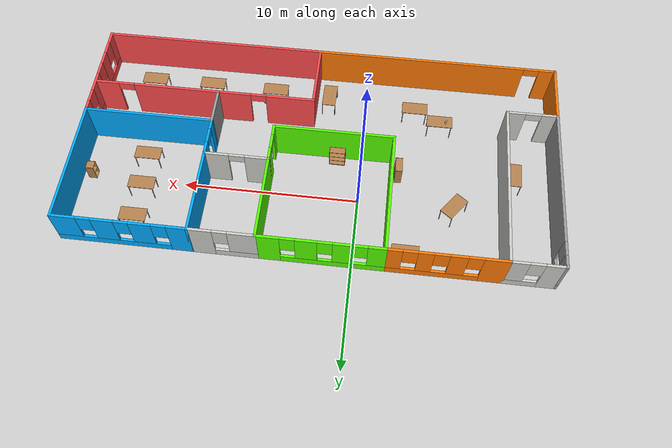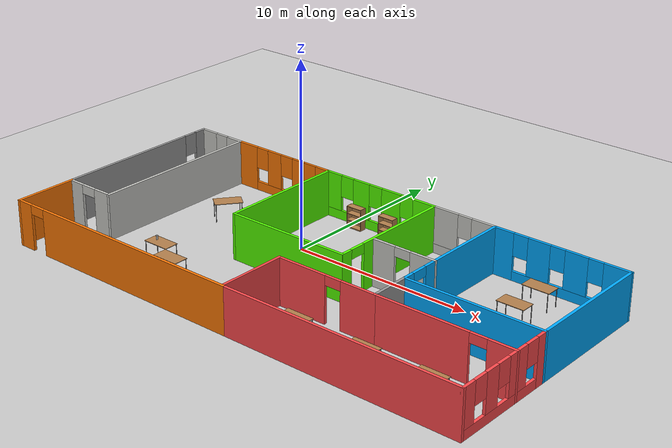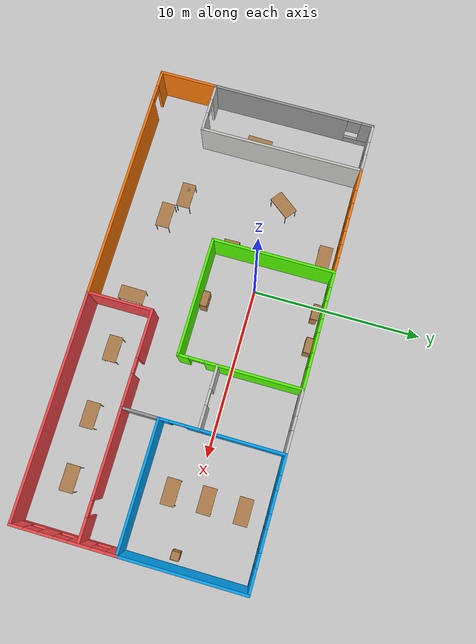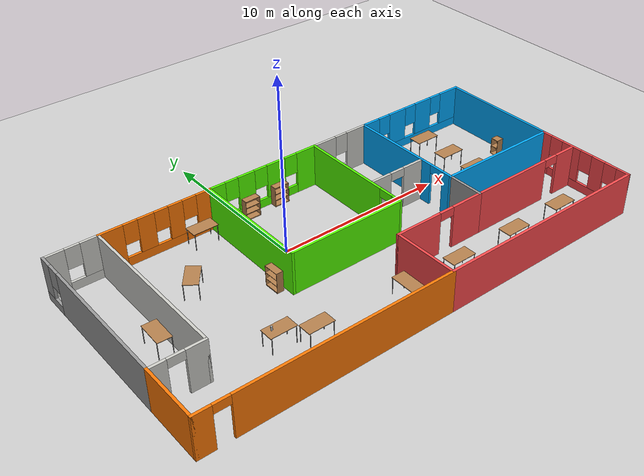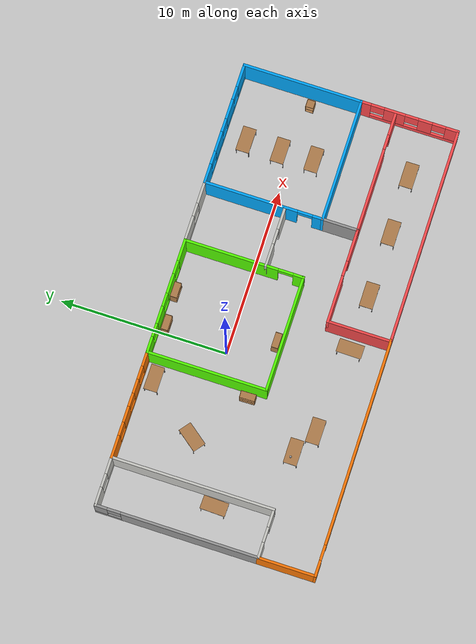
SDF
<sdf version="1.6">
 <world name="default">
  <light name="sun" type="directional">
   <pose>0 0 10 0 -0 0</pose>
   <diffuse>0.8 0.8 0.8 1</diffuse>
   <specular>0.2 0.2 0.2 1</specular>
   <attenuation>
    <range>1000</range>
    <constant>0.9</constant>
    <linear>0.01</linear>
    <quadratic>0.001</quadratic>
   </attenuation>
   <direction>-0.5 0.1 -0.9</direction>
  </light>
  <model name="ground_plane">
   <static>1</static>
   <link name="link">
    <collision name="collision">
     <geometry><plane><normal>0 0 1</normal><size>100 100</size></plane></geometry>
     <surface>
      <contact><collide_bitmask>65535</collide_bitmask></contact>
      <friction><ode><mu>100</mu><mu2>50</mu2></ode></friction>
     </surface>
    </collision>
    <visual name="visual">
     <cast_shadows>0</cast_shadows>
     <geometry><plane><normal>0 0 1</normal><size>100 100</size></plane></geometry>
     <material>
      <script><uri>file://media/materials/scripts/gazebo.material</uri><name>Gazebo/Grey</name></script>
     </material>
    </visual>
   </link>
  </model>
  <gravity>0 0 -9.8</gravity>
  <magnetic_field>6e-06 2.3e-05 -4.2e-05</magnetic_field>
  <atmosphere type="adiabatic"/>
  <physics name="default_physics" default="0" type="ode">
   <max_step_size>0.001</max_step_size>
   <real_time_factor>1</real_time_factor>
   <real_time_update_rate>1000</real_time_update_rate>
  </physics>
  <scene><ambient>0.4 0.4 0.4 1</ambient><background>0.7 0.7 0.7 1</background><shadows>1</shadows></scene>
  <spherical_coordinates>
   <surface_model>EARTH_WGS84</surface_model>
   <latitude_deg>0</latitude_deg>
   <longitude_deg>0</longitude_deg>
   <elevation>0</elevation>
   <heading_deg>0</heading_deg>
  </spherical_coordinates>
  <model name="house">
   <pose>2.5644 -2.34598 0 0 -0 0</pose>
   <link name="Wall_16">
    <collision name="Wall_16_Collision">
     <geometry><box><size>3.5 0.15 2.5</size></box></geometry>
     <pose>0 0 1.25 0 -0 0</pose>
    </collision>
    <visual name="Wall_16_Visual">
     <pose>0 0 1.25 0 -0 0</pose>
     <geometry><box><size>3.5 0.15 2.5</size></box></geometry>
     <material>
      <script><uri>file://media/materials/scripts/gazebo.material</uri><name>Gazebo/Grey</name></script>
      <ambient>0.996078 0.47451 0.0196078 1</ambient>
     </material>
     <meta><layer>0</layer></meta>
    </visual>
    <pose>-13.5 -4.79998 0 0 -0 1.5708</pose>
   </link>
   <link name="Wall_17">
    <pose>-12.075 -3.12498 0 0 -0 0</pose>
    <visual name="Wall_17_Visual_0">
     <pose>-1.01202 0 1.25 0 -0 0</pose>
     <geometry><box><size>0.97596 0.15 2.5</size></box></geometry>
     <material>
      <script><uri>file://media/materials/scripts/gazebo.material</uri><name>Gazebo/CeilingTiled</name></script>
      <ambient>1 1 1 1</ambient>
     </material>
     <meta><layer>0</layer></meta>
    </visual>
    <collision name="Wall_17_Collision_0">
     <geometry><box><size>0.97596 0.15 2.5</size></box></geometry>
     <pose>-1.01202 0 1.25 0 -0 0</pose>
    </collision>
    <visual name="Wall_17_Visual_1">
     <pose>0.93798 0 1.25 0 -0 0</pose>
     <geometry><box><size>1.12404 0.15 2.5</size></box></geometry>
     <material>
      <script><uri>file://media/materials/scripts/gazebo.material</uri><name>Gazebo/CeilingTiled</name></script>
      <ambient>1 1 1 1</ambient>
     </material>
     <meta><layer>0</layer></meta>
    </visual>
    <collision name="Wall_17_Collision_1">
     <geometry><box><size>1.12404 0.15 2.5</size></box></geometry>
     <pose>0.93798 0 1.25 0 -0 0</pose>
    </collision>
    <visual name="Wall_17_Visual_2">
     <pose>-0.07404 0 2.25 0 -0 0</pose>
     <geometry><box><size>0.9 0.15 0.5</size></box></geometry>
     <material>
      <script><uri>file://media/materials/scripts/gazebo.material</uri><name>Gazebo/CeilingTiled</name></script>
      <ambient>1 1 1 1</ambient>
     </material>
     <meta><layer>0</layer></meta>
    </visual>
    <collision name="Wall_17_Collision_2">
     <geometry><box><size>0.9 0.15 0.5</size></box></geometry>
     <pose>-0.07404 0 2.25 0 -0 0</pose>
    </collision>
   </link>
   <link name="Wall_18">
    <collision name="Wall_18_Collision">
     <geometry><box><size>9.75 0.15 2.5</size></box></geometry>
     <pose>0 0 1.25 0 -0 0</pose>
    </collision>
    <visual name="Wall_18_Visual">
     <pose>0 0 1.25 0 -0 0</pose>
     <geometry><box><size>9.75 0.15 2.5</size></box></geometry>
     <material>
      <script><uri>file://media/materials/scripts/gazebo.material</uri><name>Gazebo/CeilingTiled</name></script>
      <ambient>1 1 1 1</ambient>
     </material>
     <meta><layer>0</layer></meta>
    </visual>
    <pose>-10.65 1.67502 0 0 -0 1.5708</pose>
   </link>
   <link name="Wall_21">
    <pose>-13.5 1.67502 0 0 -0 1.5708</pose>
    <visual name="Wall_21_Visual_0">
     <pose>-0.785204 0 1.25 0 -0 0</pose>
     <geometry><box><size>8.17959 0.15 2.5</size></box></geometry>
     <material>
      <script><uri>file://media/materials/scripts/gazebo.material</uri><name>Gazebo/Grey</name></script>
      <ambient>1 1 1 1</ambient>
     </material>
     <meta><layer>0</layer></meta>
    </visual>
    <collision name="Wall_21_Collision_0">
     <geometry><box><size>8.17959 0.15 2.5</size></box></geometry>
     <pose>-0.785204 0 1.25 0 -0 0</pose>
    </collision>
    <visual name="Wall_21_Visual_1">
     <pose>4.0898 0 0.25 0 -0 0</pose>
     <geometry><box><size>1.57041 0.15 0.5</size></box></geometry>
     <material>
      <script><uri>file://media/materials/scripts/gazebo.material</uri><name>Gazebo/Grey</name></script>
      <ambient>1 1 1 1</ambient>
     </material>
     <meta><layer>0</layer></meta>
    </visual>
    <collision name="Wall_21_Collision_1">
     <geometry><box><size>1.57041 0.15 0.5</size></box></geometry>
     <pose>4.0898 0 0.25 0 -0 0</pose>
    </collision>
    <visual name="Wall_21_Visual_2">
     <pose>4.4898 0 1.5 0 -0 0</pose>
     <geometry><box><size>0.770409 0.15 2</size></box></geometry>
     <material>
      <script><uri>file://media/materials/scripts/gazebo.material</uri><name>Gazebo/Grey</name></script>
      <ambient>1 1 1 1</ambient>
     </material>
     <meta><layer>0</layer></meta>
    </visual>
    <collision name="Wall_21_Collision_2">
     <geometry><box><size>0.770409 0.15 2</size></box></geometry>
     <pose>4.4898 0 1.5 0 -0 0</pose>
    </collision>
    <visual name="Wall_21_Visual_3">
     <pose>3.70459 0 1.9 0 -0 0</pose>
     <geometry><box><size>0.8 0.15 1.2</size></box></geometry>
     <material>
      <script><uri>file://media/materials/scripts/gazebo.material</uri><name>Gazebo/Grey</name></script>
      <ambient>1 1 1 1</ambient>
     </material>
     <meta><layer>0</layer></meta>
    </visual>
    <collision name="Wall_21_Collision_3">
     <geometry><box><size>0.8 0.15 1.2</size></box></geometry>
     <pose>3.70459 0 1.9 0 -0 0</pose>
    </collision>
   </link>
   <link name="Wall_22">
    <pose>-12.075 6.47502 0 0 -0 0</pose>
    <visual name="Wall_22_Visual_0">
     <pose>-0.933912 0 1.25 0 -0 0</pose>
     <geometry><box><size>1.13217 0.15 2.5</size></box></geometry>
     <material>
      <script><uri>file://media/materials/scripts/gazebo.material</uri><name>Gazebo/CeilingTiled</name></script>
      <ambient>1 1 1 1</ambient>
     </material>
     <meta><layer>0</layer></meta>
    </visual>
    <collision name="Wall_22_Collision_0">
     <geometry><box><size>1.13217 0.15 2.5</size></box></geometry>
     <pose>-0.933912 0 1.25 0 -0 0</pose>
    </collision>
    <visual name="Wall_22_Visual_1">
     <pose>0.566088 0 0.25 0 -0 0</pose>
     <geometry><box><size>1.86783 0.15 0.5</size></box></geometry>
     <material>
      <script><uri>file://media/materials/scripts/gazebo.material</uri><name>Gazebo/CeilingTiled</name></script>
      <ambient>1 1 1 1</ambient>
     </material>
     <meta><layer>0</layer></meta>
    </visual>
    <collision name="Wall_22_Collision_1">
     <geometry><box><size>1.86783 0.15 0.5</size></box></geometry>
     <pose>0.566088 0 0.25 0 -0 0</pose>
    </collision>
    <visual name="Wall_22_Visual_2">
     <pose>0.966088 0 1.5 0 -0 0</pose>
     <geometry><box><size>1.06783 0.15 2</size></box></geometry>
     <material>
      <script><uri>file://media/materials/scripts/gazebo.material</uri><name>Gazebo/CeilingTiled</name></script>
      <ambient>1 1 1 1</ambient>
     </material>
     <meta><layer>0</layer></meta>
    </visual>
    <collision name="Wall_22_Collision_2">
     <geometry><box><size>1.06783 0.15 2</size></box></geometry>
     <pose>0.966088 0 1.5 0 -0 0</pose>
    </collision>
    <visual name="Wall_22_Visual_3">
     <pose>0.032175 0 1.9 0 -0 0</pose>
     <geometry><box><size>0.8 0.15 1.2</size></box></geometry>
     <material>
      <script><uri>file://media/materials/scripts/gazebo.material</uri><name>Gazebo/CeilingTiled</name></script>
      <ambient>1 1 1 1</ambient>
     </material>
     <meta><layer>0</layer></meta>
    </visual>
    <collision name="Wall_22_Collision_3">
     <geometry><box><size>0.8 0.15 1.2</size></box></geometry>
     <pose>0.032175 0 1.9 0 -0 0</pose>
    </collision>
   </link>
   <link name="Wall_24">
    <pose>-7.475 6.47502 0 0 -0 0</pose>
    <visual name="Wall_24_Visual_0">
     <pose>-2.56121 0 1.25 0 -0 0</pose>
     <geometry><box><size>1.37759 0.15 2.5</size></box></geometry>
     <material>
      <script><uri>file://media/materials/scripts/gazebo.material</uri><name>Gazebo/Grey</name></script>
      <ambient>0.996078 0.47451 0.0196078 1</ambient>
     </material>
     <meta><layer>0</layer></meta>
    </visual>
    <collision name="Wall_24_Collision_0">
     <geometry><box><size>1.37759 0.15 2.5</size></box></geometry>
     <pose>-2.56121 0 1.25 0 -0 0</pose>
    </collision>
    <visual name="Wall_24_Visual_1">
     <pose>0.688793 0 0.25 0 -0 0</pose>
     <geometry><box><size>5.12241 0.15 0.5</size></box></geometry>
     <material>
      <script><uri>file://media/materials/scripts/gazebo.material</uri><name>Gazebo/Grey</name></script>
      <ambient>0.996078 0.47451 0.0196078 1</ambient>
     </material>
     <meta><layer>0</layer></meta>
    </visual>
    <collision name="Wall_24_Collision_1">
     <geometry><box><size>5.12241 0.15 0.5</size></box></geometry>
     <pose>0.688793 0 0.25 0 -0 0</pose>
    </collision>
    <visual name="Wall_24_Visual_2">
     <pose>-0.600718 0 1.5 0 -0 0</pose>
     <geometry><box><size>0.943392 0.15 2</size></box></geometry>
     <material>
      <script><uri>file://media/materials/scripts/gazebo.material</uri><name>Gazebo/Grey</name></script>
      <ambient>0.996078 0.47451 0.0196078 1</ambient>
     </material>
     <meta><layer>0</layer></meta>
    </visual>
    <collision name="Wall_24_Collision_2">
     <geometry><box><size>0.943392 0.15 2</size></box></geometry>
     <pose>-0.600718 0 1.5 0 -0 0</pose>
    </collision>
    <visual name="Wall_24_Visual_3">
     <pose>1.0893 0 1.5 0 -0 0</pose>
     <geometry><box><size>0.836654 0.15 2</size></box></geometry>
     <material>
      <script><uri>file://media/materials/scripts/gazebo.material</uri><name>Gazebo/Grey</name></script>
      <ambient>0.996078 0.47451 0.0196078 1</ambient>
     </material>
     <meta><layer>0</layer></meta>
    </visual>
    <collision name="Wall_24_Collision_3">
     <geometry><box><size>0.836654 0.15 2</size></box></geometry>
     <pose>1.0893 0 1.5 0 -0 0</pose>
    </collision>
    <visual name="Wall_24_Visual_4">
     <pose>2.77882 0 1.5 0 -0 0</pose>
     <geometry><box><size>0.942368 0.15 2</size></box></geometry>
     <material>
      <script><uri>file://media/materials/scripts/gazebo.material</uri><name>Gazebo/Grey</name></script>
      <ambient>0.996078 0.47451 0.0196078 1</ambient>
     </material>
     <meta><layer>0</layer></meta>
    </visual>
    <collision name="Wall_24_Collision_4">
     <geometry><box><size>0.942368 0.15 2</size></box></geometry>
     <pose>2.77882 0 1.5 0 -0 0</pose>
    </collision>
    <visual name="Wall_24_Visual_5">
     <pose>-1.47241 0 1.9 0 -0 0</pose>
     <geometry><box><size>0.8 0.15 1.2</size></box></geometry>
     <material>
      <script><uri>file://media/materials/scripts/gazebo.material</uri><name>Gazebo/Grey</name></script>
      <ambient>0.996078 0.47451 0.0196078 1</ambient>
     </material>
     <meta><layer>0</layer></meta>
    </visual>
    <collision name="Wall_24_Collision_5">
     <geometry><box><size>0.8 0.15 1.2</size></box></geometry>
     <pose>-1.47241 0 1.9 0 -0 0</pose>
    </collision>
    <visual name="Wall_24_Visual_6">
     <pose>0.270978 0 1.9 0 -0 0</pose>
     <geometry><box><size>0.8 0.15 1.2</size></box></geometry>
     <material>
      <script><uri>file://media/materials/scripts/gazebo.material</uri><name>Gazebo/Grey</name></script>
      <ambient>0.996078 0.47451 0.0196078 1</ambient>
     </material>
     <meta><layer>0</layer></meta>
    </visual>
    <collision name="Wall_24_Collision_6">
     <geometry><box><size>0.8 0.15 1.2</size></box></geometry>
     <pose>0.270978 0 1.9 0 -0 0</pose>
    </collision>
    <visual name="Wall_24_Visual_7">
     <pose>1.90763 0 1.9 0 -0 0</pose>
     <geometry><box><size>0.8 0.15 1.2</size></box></geometry>
     <material>
      <script><uri>file://media/materials/scripts/gazebo.material</uri><name>Gazebo/Grey</name></script>
      <ambient>0.996078 0.47451 0.0196078 1</ambient>
     </material>
     <meta><layer>0</layer></meta>
    </visual>
    <collision name="Wall_24_Collision_7">
     <geometry><box><size>0.8 0.15 1.2</size></box></geometry>
     <pose>1.90763 0 1.9 0 -0 0</pose>
    </collision>
   </link>
   <link name="Wall_28">
    <collision name="Wall_28_Collision">
     <geometry><box><size>7.25 0.15 2.5</size></box></geometry>
     <pose>0 0 1.25 0 -0 0</pose>
    </collision>
    <visual name="Wall_28_Visual">
     <pose>0 0 1.25 0 -0 0</pose>
     <geometry><box><size>7.25 0.15 2.5</size></box></geometry>
     <material>
      <script><uri>file://media/materials/scripts/gazebo.material</uri><name>Gazebo/Grey</name></script>
      <ambient>0.333333 1 0 1</ambient>
     </material>
     <meta><layer>0</layer></meta>
    </visual>
    <pose>-4.3 2.92502 0 0 0 -1.5708</pose>
   </link>
   <link name="Wall_36">
    <collision name="Wall_36_Collision">
     <geometry><box><size>7 0.15 2.5</size></box></geometry>
     <pose>0 0 1.25 0 -0 0</pose>
    </collision>
    <visual name="Wall_36_Visual">
     <pose>0 0 1.25 0 -0 0</pose>
     <geometry><box><size>7 0.15 2.5</size></box></geometry>
     <material>
      <script><uri>file://media/materials/scripts/gazebo.material</uri><name>Gazebo/Grey</name></script>
      <ambient>0.333333 1 0 1</ambient>
     </material>
     <meta><layer>0</layer></meta>
    </visual>
    <pose>-0.875002 -0.624977 0 0 -0 0</pose>
   </link>
   <link name="Wall_37">
    <pose>2.55 2.92502 0 0 -0 1.5708</pose>
    <visual name="Wall_37_Visual_0">
     <pose>-3.28581 0 1.25 0 -0 0</pose>
     <geometry><box><size>0.678378 0.15 2.5</size></box></geometry>
     <material>
      <script><uri>file://media/materials/scripts/gazebo.material</uri><name>Gazebo/Grey</name></script>
      <ambient>0.333333 1 0 1</ambient>
     </material>
     <meta><layer>0</layer></meta>
    </visual>
    <collision name="Wall_37_Collision_0">
     <geometry><box><size>0.678378 0.15 2.5</size></box></geometry>
     <pose>-3.28581 0 1.25 0 -0 0</pose>
    </collision>
    <visual name="Wall_37_Visual_1">
     <pose>0.789189 0 1.25 0 -0 0</pose>
     <geometry><box><size>5.67162 0.15 2.5</size></box></geometry>
     <material>
      <script><uri>file://media/materials/scripts/gazebo.material</uri><name>Gazebo/Grey</name></script>
      <ambient>0.333333 1 0 1</ambient>
     </material>
     <meta><layer>0</layer></meta>
    </visual>
    <collision name="Wall_37_Collision_1">
     <geometry><box><size>5.67162 0.15 2.5</size></box></geometry>
     <pose>0.789189 0 1.25 0 -0 0</pose>
    </collision>
    <visual name="Wall_37_Visual_2">
     <pose>-2.49662 0 2.25 0 -0 0</pose>
     <geometry><box><size>0.9 0.15 0.5</size></box></geometry>
     <material>
      <script><uri>file://media/materials/scripts/gazebo.material</uri><name>Gazebo/Grey</name></script>
      <ambient>0.333333 1 0 1</ambient>
     </material>
     <meta><layer>0</layer></meta>
    </visual>
    <collision name="Wall_37_Collision_2">
     <geometry><box><size>0.9 0.15 0.5</size></box></geometry>
     <pose>-2.49662 0 2.25 0 -0 0</pose>
    </collision>
   </link>
   <link name="Wall_38">
    <pose>-0.875002 6.47502 0 0 -0 3.14159</pose>
    <visual name="Wall_38_Visual_0">
     <pose>-2.82375 0 1.25 0 -0 0</pose>
     <geometry><box><size>1.35249 0.15 2.5</size></box></geometry>
     <material>
      <script><uri>file://media/materials/scripts/gazebo.material</uri><name>Gazebo/Grey</name></script>
      <ambient>0.333333 1 0 1</ambient>
     </material>
     <meta><layer>0</layer></meta>
    </visual>
    <collision name="Wall_38_Collision_0">
     <geometry><box><size>1.35249 0.15 2.5</size></box></geometry>
     <pose>-2.82375 0 1.25 0 -0 0</pose>
    </collision>
    <visual name="Wall_38_Visual_1">
     <pose>0.676246 0 0.25 0 -0 0</pose>
     <geometry><box><size>5.64751 0.15 0.5</size></box></geometry>
     <material>
      <script><uri>file://media/materials/scripts/gazebo.material</uri><name>Gazebo/Grey</name></script>
      <ambient>0.333333 1 0 1</ambient>
     </material>
     <meta><layer>0</layer></meta>
    </visual>
    <collision name="Wall_38_Collision_1">
     <geometry><box><size>5.64751 0.15 0.5</size></box></geometry>
     <pose>0.676246 0 0.25 0 -0 0</pose>
    </collision>
    <visual name="Wall_38_Visual_2">
     <pose>-0.751284 0 1.5 0 -0 0</pose>
     <geometry><box><size>1.19245 0.15 2</size></box></geometry>
     <material>
      <script><uri>file://media/materials/scripts/gazebo.material</uri><name>Gazebo/Grey</name></script>
      <ambient>0.333333 1 0 1</ambient>
     </material>
     <meta><layer>0</layer></meta>
    </visual>
    <collision name="Wall_38_Collision_2">
     <geometry><box><size>1.19245 0.15 2</size></box></geometry>
     <pose>-0.751284 0 1.5 0 -0 0</pose>
    </collision>
    <visual name="Wall_38_Visual_3">
     <pose>1.17 0 1.5 0 -0 0</pose>
     <geometry><box><size>1.05013 0.15 2</size></box></geometry>
     <material>
      <script><uri>file://media/materials/scripts/gazebo.material</uri><name>Gazebo/Grey</name></script>
      <ambient>0.333333 1 0 1</ambient>
     </material>
     <meta><layer>0</layer></meta>
    </visual>
    <collision name="Wall_38_Collision_3">
     <geometry><box><size>1.05013 0.15 2</size></box></geometry>
     <pose>1.17 0 1.5 0 -0 0</pose>
    </collision>
    <visual name="Wall_38_Visual_4">
     <pose>2.99754 0 1.5 0 -0 0</pose>
     <geometry><box><size>1.00493 0.15 2</size></box></geometry>
     <material>
      <script><uri>file://media/materials/scripts/gazebo.material</uri><name>Gazebo/Grey</name></script>
      <ambient>0.333333 1 0 1</ambient>
     </material>
     <meta><layer>0</layer></meta>
    </visual>
    <collision name="Wall_38_Collision_4">
     <geometry><box><size>1.00493 0.15 2</size></box></geometry>
     <pose>2.99754 0 1.5 0 -0 0</pose>
    </collision>
    <visual name="Wall_38_Visual_5">
     <pose>-1.74751 0 1.9 0 -0 0</pose>
     <geometry><box><size>0.8 0.15 1.2</size></box></geometry>
     <material>
      <script><uri>file://media/materials/scripts/gazebo.material</uri><name>Gazebo/Grey</name></script>
      <ambient>0.333333 1 0 1</ambient>
     </material>
     <meta><layer>0</layer></meta>
    </visual>
    <collision name="Wall_38_Collision_5">
     <geometry><box><size>0.8 0.15 1.2</size></box></geometry>
     <pose>-1.74751 0 1.9 0 -0 0</pose>
    </collision>
    <visual name="Wall_38_Visual_6">
     <pose>0.24494 0 1.9 0 -0 0</pose>
     <geometry><box><size>0.8 0.15 1.2</size></box></geometry>
     <material>
      <script><uri>file://media/materials/scripts/gazebo.material</uri><name>Gazebo/Grey</name></script>
      <ambient>0.333333 1 0 1</ambient>
     </material>
     <meta><layer>0</layer></meta>
    </visual>
    <collision name="Wall_38_Collision_6">
     <geometry><box><size>0.8 0.15 1.2</size></box></geometry>
     <pose>0.24494 0 1.9 0 -0 0</pose>
    </collision>
    <visual name="Wall_38_Visual_7">
     <pose>2.09507 0 1.9 0 -0 0</pose>
     <geometry><box><size>0.8 0.15 1.2</size></box></geometry>
     <material>
      <script><uri>file://media/materials/scripts/gazebo.material</uri><name>Gazebo/Grey</name></script>
      <ambient>0.333333 1 0 1</ambient>
     </material>
     <meta><layer>0</layer></meta>
    </visual>
    <collision name="Wall_38_Collision_7">
     <geometry><box><size>0.8 0.15 1.2</size></box></geometry>
     <pose>2.09507 0 1.9 0 -0 0</pose>
    </collision>
   </link>
   <link name="Wall_42">
    <pose>4.35 6.47502 0 0 -0 3.14159</pose>
    <visual name="Wall_42_Visual_0">
     <pose>-1.17773 0 1.25 0 -0 0</pose>
     <geometry><box><size>1.39455 0.15 2.5</size></box></geometry>
     <material>
      <script><uri>file://media/materials/scripts/gazebo.material</uri><name>Gazebo/CeilingTiled</name></script>
      <ambient>1 1 1 1</ambient>
     </material>
     <meta><layer>0</layer></meta>
    </visual>
    <collision name="Wall_42_Collision_0">
     <geometry><box><size>1.39455 0.15 2.5</size></box></geometry>
     <pose>-1.17773 0 1.25 0 -0 0</pose>
    </collision>
    <visual name="Wall_42_Visual_1">
     <pose>0.697274 0 0.25 0 -0 0</pose>
     <geometry><box><size>2.35545 0.15 0.5</size></box></geometry>
     <material>
      <script><uri>file://media/materials/scripts/gazebo.material</uri><name>Gazebo/CeilingTiled</name></script>
      <ambient>1 1 1 1</ambient>
     </material>
     <meta><layer>0</layer></meta>
    </visual>
    <collision name="Wall_42_Collision_1">
     <geometry><box><size>2.35545 0.15 0.5</size></box></geometry>
     <pose>0.697274 0 0.25 0 -0 0</pose>
    </collision>
    <visual name="Wall_42_Visual_2">
     <pose>1.09727 0 1.5 0 -0 0</pose>
     <geometry><box><size>1.55545 0.15 2</size></box></geometry>
     <material>
      <script><uri>file://media/materials/scripts/gazebo.material</uri><name>Gazebo/CeilingTiled</name></script>
      <ambient>1 1 1 1</ambient>
     </material>
     <meta><layer>0</layer></meta>
    </visual>
    <collision name="Wall_42_Collision_2">
     <geometry><box><size>1.55545 0.15 2</size></box></geometry>
     <pose>1.09727 0 1.5 0 -0 0</pose>
    </collision>
    <visual name="Wall_42_Visual_3">
     <pose>-0.080451 0 1.9 0 -0 0</pose>
     <geometry><box><size>0.8 0.15 1.2</size></box></geometry>
     <material>
      <script><uri>file://media/materials/scripts/gazebo.material</uri><name>Gazebo/CeilingTiled</name></script>
      <ambient>1 1 1 1</ambient>
     </material>
     <meta><layer>0</layer></meta>
    </visual>
    <collision name="Wall_42_Collision_3">
     <geometry><box><size>0.8 0.15 1.2</size></box></geometry>
     <pose>-0.080451 0 1.9 0 -0 0</pose>
    </collision>
   </link>
   <link name="Wall_44">
    <pose>9.825 6.47502 0 0 -0 0</pose>
    <visual name="Wall_44_Visual_0">
     <pose>-3.15341 0 1.25 0 -0 0</pose>
     <geometry><box><size>1.19318 0.15 2.5</size></box></geometry>
     <material>
      <script><uri>file://media/materials/scripts/gazebo.material</uri><name>Gazebo/Grey</name></script>
      <ambient>0 0.666667 1 1</ambient>
     </material>
     <meta><layer>0</layer></meta>
    </visual>
    <collision name="Wall_44_Collision_0">
     <geometry><box><size>1.19318 0.15 2.5</size></box></geometry>
     <pose>-3.15341 0 1.25 0 -0 0</pose>
    </collision>
    <visual name="Wall_44_Visual_1">
     <pose>0.596589 0 0.25 0 -0 0</pose>
     <geometry><box><size>6.30682 0.15 0.5</size></box></geometry>
     <material>
      <script><uri>file://media/materials/scripts/gazebo.material</uri><name>Gazebo/Grey</name></script>
      <ambient>0 0.666667 1 1</ambient>
     </material>
     <meta><layer>0</layer></meta>
    </visual>
    <collision name="Wall_44_Collision_1">
     <geometry><box><size>6.30682 0.15 0.5</size></box></geometry>
     <pose>0.596589 0 0.25 0 -0 0</pose>
    </collision>
    <visual name="Wall_44_Visual_2">
     <pose>-1.14281 0 1.5 0 -0 0</pose>
     <geometry><box><size>1.22803 0.15 2</size></box></geometry>
     <material>
      <script><uri>file://media/materials/scripts/gazebo.material</uri><name>Gazebo/Grey</name></script>
      <ambient>0 0.666667 1 1</ambient>
     </material>
     <meta><layer>0</layer></meta>
    </visual>
    <collision name="Wall_44_Collision_2">
     <geometry><box><size>1.22803 0.15 2</size></box></geometry>
     <pose>-1.14281 0 1.5 0 -0 0</pose>
    </collision>
    <visual name="Wall_44_Visual_3">
     <pose>0.88522 0 1.5 0 -0 0</pose>
     <geometry><box><size>1.22803 0.15 2</size></box></geometry>
     <material>
      <script><uri>file://media/materials/scripts/gazebo.material</uri><name>Gazebo/Grey</name></script>
      <ambient>0 0.666667 1 1</ambient>
     </material>
     <meta><layer>0</layer></meta>
    </visual>
    <collision name="Wall_44_Collision_3">
     <geometry><box><size>1.22803 0.15 2</size></box></geometry>
     <pose>0.88522 0 1.5 0 -0 0</pose>
    </collision>
    <visual name="Wall_44_Visual_4">
     <pose>3.02462 0 1.5 0 -0 0</pose>
     <geometry><box><size>1.45077 0.15 2</size></box></geometry>
     <material>
      <script><uri>file://media/materials/scripts/gazebo.material</uri><name>Gazebo/Grey</name></script>
      <ambient>0 0.666667 1 1</ambient>
     </material>
     <meta><layer>0</layer></meta>
    </visual>
    <collision name="Wall_44_Collision_4">
     <geometry><box><size>1.45077 0.15 2</size></box></geometry>
     <pose>3.02462 0 1.5 0 -0 0</pose>
    </collision>
    <visual name="Wall_44_Visual_5">
     <pose>-2.15682 0 1.9 0 -0 0</pose>
     <geometry><box><size>0.8 0.15 1.2</size></box></geometry>
     <material>
      <script><uri>file://media/materials/scripts/gazebo.material</uri><name>Gazebo/Grey</name></script>
      <ambient>0 0.666667 1 1</ambient>
     </material>
     <meta><layer>0</layer></meta>
    </visual>
    <collision name="Wall_44_Collision_5">
     <geometry><box><size>0.8 0.15 1.2</size></box></geometry>
     <pose>-2.15682 0 1.9 0 -0 0</pose>
    </collision>
    <visual name="Wall_44_Visual_6">
     <pose>-0.128794 0 1.9 0 -0 0</pose>
     <geometry><box><size>0.8 0.15 1.2</size></box></geometry>
     <material>
      <script><uri>file://media/materials/scripts/gazebo.material</uri><name>Gazebo/Grey</name></script>
      <ambient>0 0.666667 1 1</ambient>
     </material>
     <meta><layer>0</layer></meta>
    </visual>
    <collision name="Wall_44_Collision_6">
     <geometry><box><size>0.8 0.15 1.2</size></box></geometry>
     <pose>-0.128794 0 1.9 0 -0 0</pose>
    </collision>
    <visual name="Wall_44_Visual_7">
     <pose>1.89923 0 1.9 0 -0 0</pose>
     <geometry><box><size>0.8 0.15 1.2</size></box></geometry>
     <material>
      <script><uri>file://media/materials/scripts/gazebo.material</uri><name>Gazebo/Grey</name></script>
      <ambient>0 0.666667 1 1</ambient>
     </material>
     <meta><layer>0</layer></meta>
    </visual>
    <collision name="Wall_44_Collision_7">
     <geometry><box><size>0.8 0.15 1.2</size></box></geometry>
     <pose>1.89923 0 1.9 0 -0 0</pose>
    </collision>
   </link>
   <link name="Wall_48">
    <collision name="Wall_48_Collision">
     <geometry><box><size>5 0.15 2.5</size></box></geometry>
     <pose>0 0 1.25 0 -0 0</pose>
    </collision>
    <visual name="Wall_48_Visual">
     <pose>0 0 1.25 0 -0 0</pose>
     <geometry><box><size>5 0.15 2.5</size></box></geometry>
     <material>
      <script><uri>file://media/materials/scripts/gazebo.material</uri><name>Gazebo/Grey</name></script>
      <ambient>0 0.666667 1 1</ambient>
     </material>
     <meta><layer>0</layer></meta>
    </visual>
    <pose>6.15 4.05002 0 0 0 -1.5708</pose>
   </link>
   <link name="Wall_50">
    <pose>4.35 1.62502 0 0 -0 3.14159</pose>
    <visual name="Wall_50_Visual_0">
     <pose>-1.15618 0 1.25 0 -0 0</pose>
     <geometry><box><size>1.43765 0.15 2.5</size></box></geometry>
     <material>
      <script><uri>file://media/materials/scripts/gazebo.material</uri><name>Gazebo/CeilingTiled</name></script>
      <ambient>1 1 1 1</ambient>
     </material>
     <meta><layer>0</layer></meta>
    </visual>
    <collision name="Wall_50_Collision_0">
     <geometry><box><size>1.43765 0.15 2.5</size></box></geometry>
     <pose>-1.15618 0 1.25 0 -0 0</pose>
    </collision>
    <visual name="Wall_50_Visual_1">
     <pose>1.16882 0 1.25 0 -0 0</pose>
     <geometry><box><size>1.41235 0.15 2.5</size></box></geometry>
     <material>
      <script><uri>file://media/materials/scripts/gazebo.material</uri><name>Gazebo/CeilingTiled</name></script>
      <ambient>1 1 1 1</ambient>
     </material>
     <meta><layer>0</layer></meta>
    </visual>
    <collision name="Wall_50_Collision_1">
     <geometry><box><size>1.41235 0.15 2.5</size></box></geometry>
     <pose>1.16882 0 1.25 0 -0 0</pose>
    </collision>
    <visual name="Wall_50_Visual_2">
     <pose>0.012646 0 2.25 0 -0 0</pose>
     <geometry><box><size>0.9 0.15 0.5</size></box></geometry>
     <material>
      <script><uri>file://media/materials/scripts/gazebo.material</uri><name>Gazebo/CeilingTiled</name></script>
      <ambient>1 1 1 1</ambient>
     </material>
     <meta><layer>0</layer></meta>
    </visual>
    <collision name="Wall_50_Collision_2">
     <geometry><box><size>0.9 0.15 0.5</size></box></geometry>
     <pose>0.012646 0 2.25 0 -0 0</pose>
    </collision>
   </link>
   <link name="Wall_52">
    <collision name="Wall_52_Collision">
     <geometry><box><size>7.25 0.15 2.5</size></box></geometry>
     <pose>0 0 1.25 0 -0 0</pose>
    </collision>
    <visual name="Wall_52_Visual">
     <pose>0 0 1.25 0 -0 0</pose>
     <geometry><box><size>7.25 0.15 2.5</size></box></geometry>
     <material>
      <script><uri>file://media/materials/scripts/gazebo.material</uri><name>Gazebo/Grey</name></script>
      <ambient>0 0.666667 1 1</ambient>
     </material>
     <meta><layer>0</layer></meta>
    </visual>
    <pose>13.4998 2.925 0 0 0 -1.57085</pose>
   </link>
   <link name="Wall_53">
    <collision name="Wall_53_Collision">
     <geometry><box><size>7.5 0.15 2.5</size></box></geometry>
     <pose>0 0 1.25 0 -0 0</pose>
    </collision>
    <visual name="Wall_53_Visual">
     <pose>0 0 1.25 0 -0 0</pose>
     <geometry><box><size>7.5 0.15 2.5</size></box></geometry>
     <material>
      <script><uri>file://media/materials/scripts/gazebo.material</uri><name>Gazebo/Grey</name></script>
      <ambient>0 0.666667 1 1</ambient>
     </material>
     <meta><layer>0</layer></meta>
    </visual>
    <pose>9.82481 -0.625 0 0 -0 3.14159</pose>
   </link>
   <link name="Wall_54">
    <pose>6.15 0.500023 0 0 -0 1.5708</pose>
    <visual name="Wall_54_Visual_0">
     <pose>-0.860811 0 1.25 0 -0 0</pose>
     <geometry><box><size>0.678378 0.15 2.5</size></box></geometry>
     <material>
      <script><uri>file://media/materials/scripts/gazebo.material</uri><name>Gazebo/Grey</name></script>
      <ambient>0 0.666667 1 1</ambient>
     </material>
     <meta><layer>0</layer></meta>
    </visual>
    <collision name="Wall_54_Collision_0">
     <geometry><box><size>0.678378 0.15 2.5</size></box></geometry>
     <pose>-0.860811 0 1.25 0 -0 0</pose>
    </collision>
    <visual name="Wall_54_Visual_1">
     <pose>0.789189 0 1.25 0 -0 0</pose>
     <geometry><box><size>0.821622 0.15 2.5</size></box></geometry>
     <material>
      <script><uri>file://media/materials/scripts/gazebo.material</uri><name>Gazebo/Grey</name></script>
      <ambient>0 0.666667 1 1</ambient>
     </material>
     <meta><layer>0</layer></meta>
    </visual>
    <collision name="Wall_54_Collision_1">
     <geometry><box><size>0.821622 0.15 2.5</size></box></geometry>
     <pose>0.789189 0 1.25 0 -0 0</pose>
    </collision>
    <visual name="Wall_54_Visual_2">
     <pose>-0.071622 0 2.25 0 -0 0</pose>
     <geometry><box><size>0.9 0.15 0.5</size></box></geometry>
     <material>
      <script><uri>file://media/materials/scripts/gazebo.material</uri><name>Gazebo/Grey</name></script>
      <ambient>0 0.666667 1 1</ambient>
     </material>
     <meta><layer>0</layer></meta>
    </visual>
    <collision name="Wall_54_Collision_2">
     <geometry><box><size>0.9 0.15 0.5</size></box></geometry>
     <pose>-0.071622 0 2.25 0 -0 0</pose>
    </collision>
   </link>
   <link name="Wall_70">
    <pose>13.4996 -3.55002 0 0 0 -1.5708</pose>
    <visual name="Wall_70_Visual_0">
     <pose>-2.66025 0 1.25 0 -0 0</pose>
     <geometry><box><size>0.67951 0.15 2.5</size></box></geometry>
     <material>
      <script><uri>file://media/materials/scripts/gazebo.material</uri><name>Gazebo/Grey</name></script>
      <ambient>1 0.290196 0.301961 1</ambient>
     </material>
     <meta><layer>0</layer></meta>
    </visual>
    <collision name="Wall_70_Collision_0">
     <geometry><box><size>0.67951 0.15 2.5</size></box></geometry>
     <pose>-2.66025 0 1.25 0 -0 0</pose>
    </collision>
    <visual name="Wall_70_Visual_1">
     <pose>0.339755 0 0.25 0 -0 0</pose>
     <geometry><box><size>5.32049 0.15 0.5</size></box></geometry>
     <material>
      <script><uri>file://media/materials/scripts/gazebo.material</uri><name>Gazebo/Grey</name></script>
      <ambient>1 0.290196 0.301961 1</ambient>
     </material>
     <meta><layer>0</layer></meta>
    </visual>
    <collision name="Wall_70_Collision_1">
     <geometry><box><size>5.32049 0.15 0.5</size></box></geometry>
     <pose>0.339755 0 0.25 0 -0 0</pose>
    </collision>
    <visual name="Wall_70_Visual_2">
     <pose>-0.888686 0 1.5 0 -0 0</pose>
     <geometry><box><size>1.26361 0.15 2</size></box></geometry>
     <material>
      <script><uri>file://media/materials/scripts/gazebo.material</uri><name>Gazebo/Grey</name></script>
      <ambient>1 0.290196 0.301961 1</ambient>
     </material>
     <meta><layer>0</layer></meta>
    </visual>
    <collision name="Wall_70_Collision_2">
     <geometry><box><size>1.26361 0.15 2</size></box></geometry>
     <pose>-0.888686 0 1.5 0 -0 0</pose>
    </collision>
    <visual name="Wall_70_Visual_3">
     <pose>0.961444 0 1.5 0 -0 0</pose>
     <geometry><box><size>0.836654 0.15 2</size></box></geometry>
     <material>
      <script><uri>file://media/materials/scripts/gazebo.material</uri><name>Gazebo/Grey</name></script>
      <ambient>1 0.290196 0.301961 1</ambient>
     </material>
     <meta><layer>0</layer></meta>
    </visual>
    <collision name="Wall_70_Collision_3">
     <geometry><box><size>0.836654 0.15 2</size></box></geometry>
     <pose>0.961444 0 1.5 0 -0 0</pose>
    </collision>
    <visual name="Wall_70_Visual_4">
     <pose>2.58989 0 1.5 0 -0 0</pose>
     <geometry><box><size>0.820229 0.15 2</size></box></geometry>
     <material>
      <script><uri>file://media/materials/scripts/gazebo.material</uri><name>Gazebo/Grey</name></script>
      <ambient>1 0.290196 0.301961 1</ambient>
     </material>
     <meta><layer>0</layer></meta>
    </visual>
    <collision name="Wall_70_Collision_4">
     <geometry><box><size>0.820229 0.15 2</size></box></geometry>
     <pose>2.58989 0 1.5 0 -0 0</pose>
    </collision>
    <visual name="Wall_70_Visual_5">
     <pose>-1.92049 0 1.9 0 -0 0</pose>
     <geometry><box><size>0.8 0.15 1.2</size></box></geometry>
     <material>
      <script><uri>file://media/materials/scripts/gazebo.material</uri><name>Gazebo/Grey</name></script>
      <ambient>1 0.290196 0.301961 1</ambient>
     </material>
     <meta><layer>0</layer></meta>
    </visual>
    <collision name="Wall_70_Collision_5">
     <geometry><box><size>0.8 0.15 1.2</size></box></geometry>
     <pose>-1.92049 0 1.9 0 -0 0</pose>
    </collision>
    <visual name="Wall_70_Visual_6">
     <pose>0.143117 0 1.9 0 -0 0</pose>
     <geometry><box><size>0.8 0.15 1.2</size></box></geometry>
     <material>
      <script><uri>file://media/materials/scripts/gazebo.material</uri><name>Gazebo/Grey</name></script>
      <ambient>1 0.290196 0.301961 1</ambient>
     </material>
     <meta><layer>0</layer></meta>
    </visual>
    <collision name="Wall_70_Collision_6">
     <geometry><box><size>0.8 0.15 1.2</size></box></geometry>
     <pose>0.143117 0 1.9 0 -0 0</pose>
    </collision>
    <visual name="Wall_70_Visual_7">
     <pose>1.77977 0 1.9 0 -0 0</pose>
     <geometry><box><size>0.8 0.15 1.2</size></box></geometry>
     <material>
      <script><uri>file://media/materials/scripts/gazebo.material</uri><name>Gazebo/Grey</name></script>
      <ambient>1 0.290196 0.301961 1</ambient>
     </material>
     <meta><layer>0</layer></meta>
    </visual>
    <collision name="Wall_70_Collision_7">
     <geometry><box><size>0.8 0.15 1.2</size></box></geometry>
     <pose>1.77977 0 1.9 0 -0 0</pose>
    </collision>
   </link>
   <link name="Wall_74">
    <collision name="Wall_74_Collision">
     <geometry><box><size>2.25 0.15 2.5</size></box></geometry>
     <pose>0 0 1.25 0 -0 0</pose>
    </collision>
    <visual name="Wall_74_Visual">
     <pose>0 0 1.25 0 -0 0</pose>
     <geometry><box><size>2.25 0.15 2.5</size></box></geometry>
     <material>
      <script><uri>file://media/materials/scripts/gazebo.material</uri><name>Gazebo/Grey</name></script>
      <ambient>1 1 1 1</ambient>
     </material>
     <meta><layer>0</layer></meta>
    </visual>
    <pose>6.15 -1.67498 0 0 0 -1.5708</pose>
   </link>
   <link name="Wall_75">
    <pose>9.825 -2.72498 0 0 -0 0</pose>
    <visual name="Wall_75_Visual_0">
     <pose>-1.19909 0 1.25 0 -0 0</pose>
     <geometry><box><size>5.10182 0.15 2.5</size></box></geometry>
     <material>
      <script><uri>file://media/materials/scripts/gazebo.material</uri><name>Gazebo/Grey</name></script>
      <ambient>1 0.290196 0.301961 1</ambient>
     </material>
     <meta><layer>0</layer></meta>
    </visual>
    <collision name="Wall_75_Collision_0">
     <geometry><box><size>5.10182 0.15 2.5</size></box></geometry>
     <pose>-1.19909 0 1.25 0 -0 0</pose>
    </collision>
    <visual name="Wall_75_Visual_1">
     <pose>3.00091 0 1.25 0 -0 0</pose>
     <geometry><box><size>1.49818 0.15 2.5</size></box></geometry>
     <material>
      <script><uri>file://media/materials/scripts/gazebo.material</uri><name>Gazebo/Grey</name></script>
      <ambient>1 0.290196 0.301961 1</ambient>
     </material>
     <meta><layer>0</layer></meta>
    </visual>
    <collision name="Wall_75_Collision_1">
     <geometry><box><size>1.49818 0.15 2.5</size></box></geometry>
     <pose>3.00091 0 1.25 0 -0 0</pose>
    </collision>
    <visual name="Wall_75_Visual_2">
     <pose>1.80182 0 2.25 0 -0 0</pose>
     <geometry><box><size>0.9 0.15 0.5</size></box></geometry>
     <material>
      <script><uri>file://media/materials/scripts/gazebo.material</uri><name>Gazebo/Grey</name></script>
      <ambient>1 0.290196 0.301961 1</ambient>
     </material>
     <meta><layer>0</layer></meta>
    </visual>
    <collision name="Wall_75_Collision_2">
     <geometry><box><size>0.9 0.15 0.5</size></box></geometry>
     <pose>1.80182 0 2.25 0 -0 0</pose>
    </collision>
   </link>
   <link name="Wall_77">
    <pose>3.35 -2.72498 0 0 -0 3.14159</pose>
    <visual name="Wall_77_Visual_0">
     <pose>-1.87906 0 1.25 0 -0 0</pose>
     <geometry><box><size>1.99187 0.15 2.5</size></box></geometry>
     <material>
      <script><uri>file://media/materials/scripts/gazebo.material</uri><name>Gazebo/Grey</name></script>
      <ambient>1 0.290196 0.301961 1</ambient>
     </material>
     <meta><layer>0</layer></meta>
    </visual>
    <collision name="Wall_77_Collision_0">
     <geometry><box><size>1.99187 0.15 2.5</size></box></geometry>
     <pose>-1.87906 0 1.25 0 -0 0</pose>
    </collision>
    <visual name="Wall_77_Visual_1">
     <pose>1.44593 0 1.25 0 -0 0</pose>
     <geometry><box><size>2.85813 0.15 2.5</size></box></geometry>
     <material>
      <script><uri>file://media/materials/scripts/gazebo.material</uri><name>Gazebo/Grey</name></script>
      <ambient>1 0.290196 0.301961 1</ambient>
     </material>
     <meta><layer>0</layer></meta>
    </visual>
    <collision name="Wall_77_Collision_1">
     <geometry><box><size>2.85813 0.15 2.5</size></box></geometry>
     <pose>1.44593 0 1.25 0 -0 0</pose>
    </collision>
    <visual name="Wall_77_Visual_2">
     <pose>-0.43313 0 2.25 0 -0 0</pose>
     <geometry><box><size>0.9 0.15 0.5</size></box></geometry>
     <material>
      <script><uri>file://media/materials/scripts/gazebo.material</uri><name>Gazebo/Grey</name></script>
      <ambient>1 0.290196 0.301961 1</ambient>
     </material>
     <meta><layer>0</layer></meta>
    </visual>
    <collision name="Wall_77_Collision_2">
     <geometry><box><size>0.9 0.15 0.5</size></box></geometry>
     <pose>-0.43313 0 2.25 0 -0 0</pose>
    </collision>
   </link>
   <link name="Wall_78">
    <collision name="Wall_78_Collision">
     <geometry><box><size>3.75 0.15 2.5</size></box></geometry>
     <pose>0 0 1.25 0 -0 0</pose>
    </collision>
    <visual name="Wall_78_Visual">
     <pose>0 0 1.25 0 -0 0</pose>
     <geometry><box><size>3.75 0.15 2.5</size></box></geometry>
     <material>
      <script><uri>file://media/materials/scripts/gazebo.material</uri><name>Gazebo/Grey</name></script>
      <ambient>0.956863 0.278431 0.286275 1</ambient>
     </material>
     <meta><layer>0</layer></meta>
    </visual>
    <pose>0.549998 -4.52498 0 0 0 -1.5708</pose>
   </link>
   <link name="Wall_80">
    <pose>-6.45 -6.47498 0 0 -0 0</pose>
    <visual name="Wall_80_Visual_0">
     <pose>-6.61949 0 1.25 0 -0 0</pose>
     <geometry><box><size>1.01102 0.15 2.5</size></box></geometry>
     <material>
      <script><uri>file://media/materials/scripts/gazebo.material</uri><name>Gazebo/Grey</name></script>
      <ambient>0.996078 0.47451 0.0196078 1</ambient>
     </material>
     <meta><layer>0</layer></meta>
    </visual>
    <collision name="Wall_80_Collision_0">
     <geometry><box><size>1.01102 0.15 2.5</size></box></geometry>
     <pose>-6.61949 0 1.25 0 -0 0</pose>
    </collision>
    <visual name="Wall_80_Visual_1">
     <pose>0.955508 0 1.25 0 -0 0</pose>
     <geometry><box><size>12.339 0.15 2.5</size></box></geometry>
     <material>
      <script><uri>file://media/materials/scripts/gazebo.material</uri><name>Gazebo/Grey</name></script>
      <ambient>0.996078 0.47451 0.0196078 1</ambient>
     </material>
     <meta><layer>0</layer></meta>
    </visual>
    <collision name="Wall_80_Collision_1">
     <geometry><box><size>12.339 0.15 2.5</size></box></geometry>
     <pose>0.955508 0 1.25 0 -0 0</pose>
    </collision>
    <visual name="Wall_80_Visual_2">
     <pose>-5.66398 0 2.25 0 -0 0</pose>
     <geometry><box><size>0.9 0.15 0.5</size></box></geometry>
     <material>
      <script><uri>file://media/materials/scripts/gazebo.material</uri><name>Gazebo/Grey</name></script>
      <ambient>0.996078 0.47451 0.0196078 1</ambient>
     </material>
     <meta><layer>0</layer></meta>
    </visual>
    <collision name="Wall_80_Collision_2">
     <geometry><box><size>0.9 0.15 0.5</size></box></geometry>
     <pose>-5.66398 0 2.25 0 -0 0</pose>
    </collision>
   </link>
   <link name="Wall_81">
    <collision name="Wall_81_Collision">
     <geometry><box><size>13.0496 0.15 2.5</size></box></geometry>
     <pose>0 0 1.25 0 -0 0</pose>
    </collision>
    <visual name="Wall_81_Visual">
     <pose>0 0 1.25 0 -0 0</pose>
     <geometry><box><size>13.0496 0.15 2.5</size></box></geometry>
     <material>
      <script><uri>file://media/materials/scripts/gazebo.material</uri><name>Gazebo/Grey</name></script>
      <ambient>1 0.290196 0.301961 1</ambient>
     </material>
     <meta><layer>0</layer></meta>
    </visual>
    <pose>7.04981 -6.475 0 0 0 -4e-06</pose>
   </link>
   <static>1</static>
  </model>
  <model name="table">
   <static>1</static>
   <link name="link">
    <collision name="surface">
     <pose>0 0 1 0 -0 0</pose>
     <geometry><box><size>1.5 0.8 0.03</size></box></geometry>
     <surface><friction><ode><mu>0.6</mu><mu2>0.6</mu2></ode></friction></surface>
    </collision>
    <visual name="visual1">
     <pose>0 0 1 0 -0 0</pose>
     <geometry><box><size>1.5 0.8 0.03</size></box></geometry>
     <material>
      <script><uri>file://media/materials/scripts/gazebo.material</uri><name>Gazebo/Wood</name></script>
     </material>
    </visual>
    <collision name="front_left_leg">
     <pose>0.68 0.38 0.5 0 -0 0</pose>
     <geometry><cylinder><radius>0.02</radius><length>1</length></cylinder></geometry>
    </collision>
    <visual name="front_left_leg">
     <pose>0.68 0.38 0.5 0 -0 0</pose>
     <geometry><cylinder><radius>0.02</radius><length>1</length></cylinder></geometry>
     <material>
      <script><uri>file://media/materials/scripts/gazebo.material</uri><name>Gazebo/Grey</name></script>
     </material>
    </visual>
    <collision name="front_right_leg">
     <pose>0.68 -0.38 0.5 0 -0 0</pose>
     <geometry><cylinder><radius>0.02</radius><length>1</length></cylinder></geometry>
    </collision>
    <visual name="front_right_leg">
     <pose>0.68 -0.38 0.5 0 -0 0</pose>
     <geometry><cylinder><radius>0.02</radius><length>1</length></cylinder></geometry>
     <material>
      <script><uri>file://media/materials/scripts/gazebo.material</uri><name>Gazebo/Grey</name></script>
     </material>
    </visual>
    <collision name="back_right_leg">
     <pose>-0.68 -0.38 0.5 0 -0 0</pose>
     <geometry><cylinder><radius>0.02</radius><length>1</length></cylinder></geometry>
    </collision>
    <visual name="back_right_leg">
     <pose>-0.68 -0.38 0.5 0 -0 0</pose>
     <geometry><cylinder><radius>0.02</radius><length>1</length></cylinder></geometry>
     <material>
      <script><uri>file://media/materials/scripts/gazebo.material</uri><name>Gazebo/Grey</name></script>
     </material>
    </visual>
    <collision name="back_left_leg">
     <pose>-0.68 0.38 0.5 0 -0 0</pose>
     <geometry><cylinder><radius>0.02</radius><length>1</length></cylinder></geometry>
    </collision>
    <visual name="back_left_leg">
     <pose>-0.68 0.38 0.5 0 -0 0</pose>
     <geometry><cylinder><radius>0.02</radius><length>1</length></cylinder></geometry>
     <material>
      <script><uri>file://media/materials/scripts/gazebo.material</uri><name>Gazebo/Grey</name></script>
     </material>
    </visual>
   </link>
   <pose>-5.37303 0.274904 0 0 0 -2.22515</pose>
  </model>
  <model name="table_0">
   <static>1</static>
   <link name="link">
    <collision name="surface">
     <pose>0 0 1 0 -0 0</pose>
     <geometry><box><size>1.5 0.8 0.03</size></box></geometry>
     <surface><friction><ode><mu>0.6</mu><mu2>0.6</mu2></ode></friction></surface>
    </collision>
    <visual name="visual1">
     <pose>0 0 1 0 -0 0</pose>
     <geometry><box><size>1.5 0.8 0.03</size></box></geometry>
     <material>
      <script><uri>file://media/materials/scripts/gazebo.material</uri><name>Gazebo/Wood</name></script>
     </material>
    </visual>
    <collision name="front_left_leg">
     <pose>0.68 0.38 0.5 0 -0 0</pose>
     <geometry><cylinder><radius>0.02</radius><length>1</length></cylinder></geometry>
    </collision>
    <visual name="front_left_leg">
     <pose>0.68 0.38 0.5 0 -0 0</pose>
     <geometry><cylinder><radius>0.02</radius><length>1</length></cylinder></geometry>
     <material>
      <script><uri>file://media/materials/scripts/gazebo.material</uri><name>Gazebo/Grey</name></script>
     </material>
    </visual>
    <collision name="front_right_leg">
     <pose>0.68 -0.38 0.5 0 -0 0</pose>
     <geometry><cylinder><radius>0.02</radius><length>1</length></cylinder></geometry>
    </collision>
    <visual name="front_right_leg">
     <pose>0.68 -0.38 0.5 0 -0 0</pose>
     <geometry><cylinder><radius>0.02</radius><length>1</length></cylinder></geometry>
     <material>
      <script><uri>file://media/materials/scripts/gazebo.material</uri><name>Gazebo/Grey</name></script>
     </material>
    </visual>
    <collision name="back_right_leg">
     <pose>-0.68 -0.38 0.5 0 -0 0</pose>
     <geometry><cylinder><radius>0.02</radius><length>1</length></cylinder></geometry>
    </collision>
    <visual name="back_right_leg">
     <pose>-0.68 -0.38 0.5 0 -0 0</pose>
     <geometry><cylinder><radius>0.02</radius><length>1</length></cylinder></geometry>
     <material>
      <script><uri>file://media/materials/scripts/gazebo.material</uri><name>Gazebo/Grey</name></script>
     </material>
    </visual>
    <collision name="back_left_leg">
     <pose>-0.68 0.38 0.5 0 -0 0</pose>
     <geometry><cylinder><radius>0.02</radius><length>1</length></cylinder></geometry>
    </collision>
    <visual name="back_left_leg">
     <pose>-0.68 0.38 0.5 0 -0 0</pose>
     <geometry><cylinder><radius>0.02</radius><length>1</length></cylinder></geometry>
     <material>
      <script><uri>file://media/materials/scripts/gazebo.material</uri><name>Gazebo/Grey</name></script>
     </material>
    </visual>
   </link>
   <pose>-2.87312 -6.30679 0 0 -0 0</pose>
  </model>
  <model name="table_1">
   <static>1</static>
   <link name="link">
    <collision name="surface">
     <pose>0 0 1 0 -0 0</pose>
     <geometry><box><size>1.5 0.8 0.03</size></box></geometry>
     <surface><friction><ode><mu>0.6</mu><mu2>0.6</mu2></ode></friction></surface>
    </collision>
    <visual name="visual1">
     <pose>0 0 1 0 -0 0</pose>
     <geometry><box><size>1.5 0.8 0.03</size></box></geometry>
     <material>
      <script><uri>file://media/materials/scripts/gazebo.material</uri><name>Gazebo/Wood</name></script>
     </material>
    </visual>
    <collision name="front_left_leg">
     <pose>0.68 0.38 0.5 0 -0 0</pose>
     <geometry><cylinder><radius>0.02</radius><length>1</length></cylinder></geometry>
    </collision>
    <visual name="front_left_leg">
     <pose>0.68 0.38 0.5 0 -0 0</pose>
     <geometry><cylinder><radius>0.02</radius><length>1</length></cylinder></geometry>
     <material>
      <script><uri>file://media/materials/scripts/gazebo.material</uri><name>Gazebo/Grey</name></script>
     </material>
    </visual>
    <collision name="front_right_leg">
     <pose>0.68 -0.38 0.5 0 -0 0</pose>
     <geometry><cylinder><radius>0.02</radius><length>1</length></cylinder></geometry>
    </collision>
    <visual name="front_right_leg">
     <pose>0.68 -0.38 0.5 0 -0 0</pose>
     <geometry><cylinder><radius>0.02</radius><length>1</length></cylinder></geometry>
     <material>
      <script><uri>file://media/materials/scripts/gazebo.material</uri><name>Gazebo/Grey</name></script>
     </material>
    </visual>
    <collision name="back_right_leg">
     <pose>-0.68 -0.38 0.5 0 -0 0</pose>
     <geometry><cylinder><radius>0.02</radius><length>1</length></cylinder></geometry>
    </collision>
    <visual name="back_right_leg">
     <pose>-0.68 -0.38 0.5 0 -0 0</pose>
     <geometry><cylinder><radius>0.02</radius><length>1</length></cylinder></geometry>
     <material>
      <script><uri>file://media/materials/scripts/gazebo.material</uri><name>Gazebo/Grey</name></script>
     </material>
    </visual>
    <collision name="back_left_leg">
     <pose>-0.68 0.38 0.5 0 -0 0</pose>
     <geometry><cylinder><radius>0.02</radius><length>1</length></cylinder></geometry>
    </collision>
    <visual name="back_left_leg">
     <pose>-0.68 0.38 0.5 0 -0 0</pose>
     <geometry><cylinder><radius>0.02</radius><length>1</length></cylinder></geometry>
     <material>
      <script><uri>file://media/materials/scripts/gazebo.material</uri><name>Gazebo/Grey</name></script>
     </material>
    </visual>
   </link>
   <pose>-2.80982 3.3973 0 0 -0 0</pose>
  </model>
  <model name="table_2">
   <static>1</static>
   <link name="link">
    <collision name="surface">
     <pose>0 0 1 0 -0 0</pose>
     <geometry><box><size>1.5 0.8 0.03</size></box></geometry>
     <surface><friction><ode><mu>0.6</mu><mu2>0.6</mu2></ode></friction></surface>
    </collision>
    <visual name="visual1">
     <pose>0 0 1 0 -0 0</pose>
     <geometry><box><size>1.5 0.8 0.03</size></box></geometry>
     <material>
      <script><uri>file://media/materials/scripts/gazebo.material</uri><name>Gazebo/Wood</name></script>
     </material>
    </visual>
    <collision name="front_left_leg">
     <pose>0.68 0.38 0.5 0 -0 0</pose>
     <geometry><cylinder><radius>0.02</radius><length>1</length></cylinder></geometry>
    </collision>
    <visual name="front_left_leg">
     <pose>0.68 0.38 0.5 0 -0 0</pose>
     <geometry><cylinder><radius>0.02</radius><length>1</length></cylinder></geometry>
     <material>
      <script><uri>file://media/materials/scripts/gazebo.material</uri><name>Gazebo/Grey</name></script>
     </material>
    </visual>
    <collision name="front_right_leg">
     <pose>0.68 -0.38 0.5 0 -0 0</pose>
     <geometry><cylinder><radius>0.02</radius><length>1</length></cylinder></geometry>
    </collision>
    <visual name="front_right_leg">
     <pose>0.68 -0.38 0.5 0 -0 0</pose>
     <geometry><cylinder><radius>0.02</radius><length>1</length></cylinder></geometry>
     <material>
      <script><uri>file://media/materials/scripts/gazebo.material</uri><name>Gazebo/Grey</name></script>
     </material>
    </visual>
    <collision name="back_right_leg">
     <pose>-0.68 -0.38 0.5 0 -0 0</pose>
     <geometry><cylinder><radius>0.02</radius><length>1</length></cylinder></geometry>
    </collision>
    <visual name="back_right_leg">
     <pose>-0.68 -0.38 0.5 0 -0 0</pose>
     <geometry><cylinder><radius>0.02</radius><length>1</length></cylinder></geometry>
     <material>
      <script><uri>file://media/materials/scripts/gazebo.material</uri><name>Gazebo/Grey</name></script>
     </material>
    </visual>
    <collision name="back_left_leg">
     <pose>-0.68 0.38 0.5 0 -0 0</pose>
     <geometry><cylinder><radius>0.02</radius><length>1</length></cylinder></geometry>
    </collision>
    <visual name="back_left_leg">
     <pose>-0.68 0.38 0.5 0 -0 0</pose>
     <geometry><cylinder><radius>0.02</radius><length>1</length></cylinder></geometry>
     <material>
      <script><uri>file://media/materials/scripts/gazebo.material</uri><name>Gazebo/Grey</name></script>
     </material>
    </visual>
   </link>
   <pose>-4.38739 -5.47523 0 0 -0 0</pose>
  </model>
  <model name="table_3">
   <static>1</static>
   <link name="link">
    <collision name="surface">
     <pose>0 0 1 0 -0 0</pose>
     <geometry><box><size>1.5 0.8 0.03</size></box></geometry>
     <surface><friction><ode><mu>0.6</mu><mu2>0.6</mu2></ode></friction></surface>
    </collision>
    <visual name="visual1">
     <pose>0 0 1 0 -0 0</pose>
     <geometry><box><size>1.5 0.8 0.03</size></box></geometry>
     <material>
      <script><uri>file://media/materials/scripts/gazebo.material</uri><name>Gazebo/Wood</name></script>
     </material>
    </visual>
    <collision name="front_left_leg">
     <pose>0.68 0.38 0.5 0 -0 0</pose>
     <geometry><cylinder><radius>0.02</radius><length>1</length></cylinder></geometry>
    </collision>
    <visual name="front_left_leg">
     <pose>0.68 0.38 0.5 0 -0 0</pose>
     <geometry><cylinder><radius>0.02</radius><length>1</length></cylinder></geometry>
     <material>
      <script><uri>file://media/materials/scripts/gazebo.material</uri><name>Gazebo/Grey</name></script>
     </material>
    </visual>
    <collision name="front_right_leg">
     <pose>0.68 -0.38 0.5 0 -0 0</pose>
     <geometry><cylinder><radius>0.02</radius><length>1</length></cylinder></geometry>
    </collision>
    <visual name="front_right_leg">
     <pose>0.68 -0.38 0.5 0 -0 0</pose>
     <geometry><cylinder><radius>0.02</radius><length>1</length></cylinder></geometry>
     <material>
      <script><uri>file://media/materials/scripts/gazebo.material</uri><name>Gazebo/Grey</name></script>
     </material>
    </visual>
    <collision name="back_right_leg">
     <pose>-0.68 -0.38 0.5 0 -0 0</pose>
     <geometry><cylinder><radius>0.02</radius><length>1</length></cylinder></geometry>
    </collision>
    <visual name="back_right_leg">
     <pose>-0.68 -0.38 0.5 0 -0 0</pose>
     <geometry><cylinder><radius>0.02</radius><length>1</length></cylinder></geometry>
     <material>
      <script><uri>file://media/materials/scripts/gazebo.material</uri><name>Gazebo/Grey</name></script>
     </material>
    </visual>
    <collision name="back_left_leg">
     <pose>-0.68 0.38 0.5 0 -0 0</pose>
     <geometry><cylinder><radius>0.02</radius><length>1</length></cylinder></geometry>
    </collision>
    <visual name="back_left_leg">
     <pose>-0.68 0.38 0.5 0 -0 0</pose>
     <geometry><cylinder><radius>0.02</radius><length>1</length></cylinder></geometry>
     <material>
      <script><uri>file://media/materials/scripts/gazebo.material</uri><name>Gazebo/Grey</name></script>
     </material>
    </visual>
   </link>
   <pose>-8.73159 -2.16161 0 0 0 -1.59924</pose>
  </model>
  <model name="beer">
   <link name="link">
    <pose>0 0 0.115 0 -0 0</pose>
    <inertial>
     <mass>0.39</mass>
     <inertia><ixx>0.00058</ixx><ixy>0</ixy><ixz>0</ixz><iyy>0.00058</iyy><iyz>0</iyz><izz>0.00019</izz></inertia>
    </inertial>
    <collision name="collision">
     <geometry><cylinder><radius>0.055</radius><length>0.23</length></cylinder></geometry>
    </collision>
    <visual name="visual">
     <geometry><cylinder><radius>0.055</radius><length>0.23</length></cylinder></geometry>
     <material>
      <script>
       <uri>model://beer/materials/scripts</uri>
       <uri>model://beer/materials/textures</uri>
       <name>Beer/Diffuse</name>
      </script>
     </material>
    </visual>
   </link>
   <pose>-4.73816 -5.39807 1.01499 2e-06 -2.7e-05 0.00187</pose>
  </model>
  <model name="bookshelf">
   <static>1</static>
   <link name="link">
    <inertial><mass>1</mass></inertial>
    <collision name="back">
     <pose>0 0.005 0.6 0 -0 0</pose>
     <geometry><box><size>0.9 0.01 1.2</size></box></geometry>
    </collision>
    <visual name="visual1">
     <pose>0 0.005 0.6 0 -0 0</pose>
     <geometry><box><size>0.9 0.01 1.2</size></box></geometry>
     <material>
      <script><uri>file://media/materials/scripts/gazebo.material</uri><name>Gazebo/Wood</name></script>
     </material>
    </visual>
    <collision name="left_side">
     <pose>0.45 -0.195 0.6 0 -0 0</pose>
     <geometry><box><size>0.02 0.4 1.2</size></box></geometry>
    </collision>
    <visual name="visual2">
     <pose>0.45 -0.195 0.6 0 -0 0</pose>
     <geometry><box><size>0.02 0.4 1.2</size></box></geometry>
     <material>
      <script><uri>file://media/materials/scripts/gazebo.material</uri><name>Gazebo/Wood</name></script>
     </material>
    </visual>
    <collision name="right_side">
     <pose>-0.45 -0.195 0.6 0 -0 0</pose>
     <geometry><box><size>0.02 0.4 1.2</size></box></geometry>
    </collision>
    <visual name="visual3">
     <pose>-0.45 -0.195 0.6 0 -0 0</pose>
     <geometry><box><size>0.02 0.4 1.2</size></box></geometry>
     <material>
      <script><uri>file://media/materials/scripts/gazebo.material</uri><name>Gazebo/Wood</name></script>
     </material>
    </visual>
    <collision name="bottom">
     <pose>0 -0.195 0.03 0 -0 0</pose>
     <geometry><box><size>0.88 0.4 0.06</size></box></geometry>
    </collision>
    <visual name="visual4">
     <pose>0 -0.195 0.03 0 -0 0</pose>
     <geometry><box><size>0.88 0.4 0.06</size></box></geometry>
     <material>
      <script><uri>file://media/materials/scripts/gazebo.material</uri><name>Gazebo/Wood</name></script>
     </material>
    </visual>
    <collision name="top">
     <pose>0 -0.195 1.19 0 -0 0</pose>
     <geometry><box><size>0.88 0.4 0.02</size></box></geometry>
    </collision>
    <visual name="visual5">
     <pose>0 -0.195 1.19 0 -0 0</pose>
     <geometry><box><size>0.88 0.4 0.02</size></box></geometry>
     <material>
      <script><uri>file://media/materials/scripts/gazebo.material</uri><name>Gazebo/Wood</name></script>
     </material>
    </visual>
    <collision name="low_shelf">
     <pose>0 -0.195 0.43 0 -0 0</pose>
     <geometry><box><size>0.88 0.4 0.02</size></box></geometry>
    </collision>
    <visual name="visual6">
     <pose>0 -0.195 0.43 0 -0 0</pose>
     <geometry><box><size>0.88 0.4 0.02</size></box></geometry>
     <material>
      <script><uri>file://media/materials/scripts/gazebo.material</uri><name>Gazebo/Wood</name></script>
     </material>
    </visual>
    <collision name="high_shelf">
     <pose>0 -0.195 0.8 0 -0 0</pose>
     <geometry><box><size>0.88 0.4 0.02</size></box></geometry>
    </collision>
    <visual name="visual7">
     <pose>0 -0.195 0.8 0 -0 0</pose>
     <geometry><box><size>0.88 0.4 0.02</size></box></geometry>
     <material>
      <script><uri>file://media/materials/scripts/gazebo.material</uri><name>Gazebo/Wood</name></script>
     </material>
    </visual>
   </link>
   <pose>0.469107 3.9315 0 0 -0 0</pose>
  </model>
  <model name="bookshelf_0">
   <static>1</static>
   <link name="link">
    <inertial><mass>1</mass></inertial>
    <collision name="back">
     <pose>0 0.005 0.6 0 -0 0</pose>
     <geometry><box><size>0.9 0.01 1.2</size></box></geometry>
    </collision>
    <visual name="visual1">
     <pose>0 0.005 0.6 0 -0 0</pose>
     <geometry><box><size>0.9 0.01 1.2</size></box></geometry>
     <material>
      <script><uri>file://media/materials/scripts/gazebo.material</uri><name>Gazebo/Wood</name></script>
     </material>
    </visual>
    <collision name="left_side">
     <pose>0.45 -0.195 0.6 0 -0 0</pose>
     <geometry><box><size>0.02 0.4 1.2</size></box></geometry>
    </collision>
    <visual name="visual2">
     <pose>0.45 -0.195 0.6 0 -0 0</pose>
     <geometry><box><size>0.02 0.4 1.2</size></box></geometry>
     <material>
      <script><uri>file://media/materials/scripts/gazebo.material</uri><name>Gazebo/Wood</name></script>
     </material>
    </visual>
    <collision name="right_side">
     <pose>-0.45 -0.195 0.6 0 -0 0</pose>
     <geometry><box><size>0.02 0.4 1.2</size></box></geometry>
    </collision>
    <visual name="visual3">
     <pose>-0.45 -0.195 0.6 0 -0 0</pose>
     <geometry><box><size>0.02 0.4 1.2</size></box></geometry>
     <material>
      <script><uri>file://media/materials/scripts/gazebo.material</uri><name>Gazebo/Wood</name></script>
     </material>
    </visual>
    <collision name="bottom">
     <pose>0 -0.195 0.03 0 -0 0</pose>
     <geometry><box><size>0.88 0.4 0.06</size></box></geometry>
    </collision>
    <visual name="visual4">
     <pose>0 -0.195 0.03 0 -0 0</pose>
     <geometry><box><size>0.88 0.4 0.06</size></box></geometry>
     <material>
      <script><uri>file://media/materials/scripts/gazebo.material</uri><name>Gazebo/Wood</name></script>
     </material>
    </visual>
    <collision name="top">
     <pose>0 -0.195 1.19 0 -0 0</pose>
     <geometry><box><size>0.88 0.4 0.02</size></box></geometry>
    </collision>
    <visual name="visual5">
     <pose>0 -0.195 1.19 0 -0 0</pose>
     <geometry><box><size>0.88 0.4 0.02</size></box></geometry>
     <material>
      <script><uri>file://media/materials/scripts/gazebo.material</uri><name>Gazebo/Wood</name></script>
     </material>
    </visual>
    <collision name="low_shelf">
     <pose>0 -0.195 0.43 0 -0 0</pose>
     <geometry><box><size>0.88 0.4 0.02</size></box></geometry>
    </collision>
    <visual name="visual6">
     <pose>0 -0.195 0.43 0 -0 0</pose>
     <geometry><box><size>0.88 0.4 0.02</size></box></geometry>
     <material>
      <script><uri>file://media/materials/scripts/gazebo.material</uri><name>Gazebo/Wood</name></script>
     </material>
    </visual>
    <collision name="high_shelf">
     <pose>0 -0.195 0.8 0 -0 0</pose>
     <geometry><box><size>0.88 0.4 0.02</size></box></geometry>
    </collision>
    <visual name="visual7">
     <pose>0 -0.195 0.8 0 -0 0</pose>
     <geometry><box><size>0.88 0.4 0.02</size></box></geometry>
     <material>
      <script><uri>file://media/materials/scripts/gazebo.material</uri><name>Gazebo/Wood</name></script>
     </material>
    </visual>
   </link>
   <pose>2.44857 4.02681 0 0 -0 0</pose>
  </model>
  <model name="cabinet">
   <static>1</static>
   <link name="cabinet_bottom_plate">
    <inertial>
     <pose>0 0 -1 0 -0 0</pose>
     <inertia><ixx>2.05</ixx><ixy>0</ixy><ixz>0</ixz><iyy>2.05</iyy><iyz>0</iyz><izz>2.05</izz></inertia>
     <mass>25</mass>
    </inertial>
    <collision name="cabinet_bottom_plate_geom">
     <pose>0 0 0.01 0 -0 0</pose>
     <geometry><box><size>0.45 0.45 0.02</size></box></geometry>
    </collision>
    <visual name="cabinet_bottom_plate_geom_visual">
     <pose>0 0 0.01 0 -0 0</pose>
     <geometry><box><size>0.45 0.45 0.02</size></box></geometry>
     <material>
      <script><uri>file://media/materials/scripts/gazebo.material</uri><name>Gazebo/Wood</name></script>
     </material>
    </visual>
    <collision name="cabinet_bottom_plate_geom_cabinet_back_plate">
     <pose>0.235 0 0.51 0 -0 0</pose>
     <geometry><box><size>0.02 0.45 1.02</size></box></geometry>
    </collision>
    <visual name="cabinet_bottom_plate_geom_cabinet_back_plate_visual">
     <pose>0.235 0 0.51 0 -0 0</pose>
     <geometry><box><size>0.02 0.45 1.02</size></box></geometry>
     <material>
      <script><uri>file://media/materials/scripts/gazebo.material</uri><name>Gazebo/Wood</name></script>
     </material>
    </visual>
    <collision name="cabinet_bottom_plate_geom_cabinet_left_plate">
     <pose>0 0.235 0.51 0 -0 0</pose>
     <geometry><box><size>0.45 0.02 1.02</size></box></geometry>
    </collision>
    <visual name="cabinet_bottom_plate_geom_cabinet_left_plate_visual">
     <pose>0 0.235 0.51 0 -0 0</pose>
     <geometry><box><size>0.45 0.02 1.02</size></box></geometry>
     <material>
      <script><uri>file://media/materials/scripts/gazebo.material</uri><name>Gazebo/Wood</name></script>
     </material>
    </visual>
    <collision name="cabinet_bottom_plate_geom_cabinet_middle_plate">
     <pose>0 0 0.51 0 -0 0</pose>
     <geometry><box><size>0.45 0.45 0.02</size></box></geometry>
    </collision>
    <visual name="cabinet_bottom_plate_geom_cabinet_middle_plate_visual">
     <pose>0 0 0.51 0 -0 0</pose>
     <geometry><box><size>0.45 0.45 0.02</size></box></geometry>
     <material>
      <script><uri>file://media/materials/scripts/gazebo.material</uri><name>Gazebo/Wood</name></script>
     </material>
    </visual>
    <collision name="cabinet_bottom_plate_geom_cabinet_right_plate">
     <pose>0 -0.235 0.51 0 -0 0</pose>
     <geometry><box><size>0.45 0.02 1.02</size></box></geometry>
    </collision>
    <visual name="cabinet_bottom_plate_geom_cabinet_right_plate_visual">
     <pose>0 -0.235 0.51 0 -0 0</pose>
     <geometry><box><size>0.45 0.02 1.02</size></box></geometry>
     <material>
      <script><uri>file://media/materials/scripts/gazebo.material</uri><name>Gazebo/Wood</name></script>
     </material>
    </visual>
    <collision name="cabinet_bottom_plate_geom_cabinet_top_plate">
     <pose>0 0 1.01 0 -0 0</pose>
     <geometry><box><size>0.45 0.45 0.02</size></box></geometry>
    </collision>
    <visual name="cabinet_bottom_plate_geom_cabinet_top_plate_visual">
     <pose>0 0 1.01 0 -0 0</pose>
     <geometry><box><size>0.45 0.45 0.02</size></box></geometry>
     <material>
      <script><uri>file://media/materials/scripts/gazebo.material</uri><name>Gazebo/Wood</name></script>
     </material>
    </visual>
   </link>
   <pose>15.4217 -0.13321 0 0 -0 0</pose>
  </model>
  <model name="table_4">
   <static>1</static>
   <link name="link">
    <collision name="surface">
     <pose>0 0 1 0 -0 0</pose>
     <geometry><box><size>1.5 0.8 0.03</size></box></geometry>
     <surface><friction><ode><mu>0.6</mu><mu2>0.6</mu2></ode></friction></surface>
    </collision>
    <visual name="visual1">
     <pose>0 0 1 0 -0 0</pose>
     <geometry><box><size>1.5 0.8 0.03</size></box></geometry>
     <material>
      <script><uri>file://media/materials/scripts/gazebo.material</uri><name>Gazebo/Wood</name></script>
     </material>
    </visual>
    <collision name="front_left_leg">
     <pose>0.68 0.38 0.5 0 -0 0</pose>
     <geometry><cylinder><radius>0.02</radius><length>1</length></cylinder></geometry>
    </collision>
    <visual name="front_left_leg">
     <pose>0.68 0.38 0.5 0 -0 0</pose>
     <geometry><cylinder><radius>0.02</radius><length>1</length></cylinder></geometry>
     <material>
      <script><uri>file://media/materials/scripts/gazebo.material</uri><name>Gazebo/Grey</name></script>
     </material>
    </visual>
    <collision name="front_right_leg">
     <pose>0.68 -0.38 0.5 0 -0 0</pose>
     <geometry><cylinder><radius>0.02</radius><length>1</length></cylinder></geometry>
    </collision>
    <visual name="front_right_leg">
     <pose>0.68 -0.38 0.5 0 -0 0</pose>
     <geometry><cylinder><radius>0.02</radius><length>1</length></cylinder></geometry>
     <material>
      <script><uri>file://media/materials/scripts/gazebo.material</uri><name>Gazebo/Grey</name></script>
     </material>
    </visual>
    <collision name="back_right_leg">
     <pose>-0.68 -0.38 0.5 0 -0 0</pose>
     <geometry><cylinder><radius>0.02</radius><length>1</length></cylinder></geometry>
    </collision>
    <visual name="back_right_leg">
     <pose>-0.68 -0.38 0.5 0 -0 0</pose>
     <geometry><cylinder><radius>0.02</radius><length>1</length></cylinder></geometry>
     <material>
      <script><uri>file://media/materials/scripts/gazebo.material</uri><name>Gazebo/Grey</name></script>
     </material>
    </visual>
    <collision name="back_left_leg">
     <pose>-0.68 0.38 0.5 0 -0 0</pose>
     <geometry><cylinder><radius>0.02</radius><length>1</length></cylinder></geometry>
    </collision>
    <visual name="back_left_leg">
     <pose>-0.68 0.38 0.5 0 -0 0</pose>
     <geometry><cylinder><radius>0.02</radius><length>1</length></cylinder></geometry>
     <material>
      <script><uri>file://media/materials/scripts/gazebo.material</uri><name>Gazebo/Grey</name></script>
     </material>
    </visual>
   </link>
   <pose>12.221 2.77174 0 0 -0 0</pose>
  </model>
  <model name="table_5">
   <static>1</static>
   <link name="link">
    <collision name="surface">
     <pose>0 0 1 0 -0 0</pose>
     <geometry><box><size>1.5 0.8 0.03</size></box></geometry>
     <surface><friction><ode><mu>0.6</mu><mu2>0.6</mu2></ode></friction></surface>
    </collision>
    <visual name="visual1">
     <pose>0 0 1 0 -0 0</pose>
     <geometry><box><size>1.5 0.8 0.03</size></box></geometry>
     <material>
      <script><uri>file://media/materials/scripts/gazebo.material</uri><name>Gazebo/Wood</name></script>
     </material>
    </visual>
    <collision name="front_left_leg">
     <pose>0.68 0.38 0.5 0 -0 0</pose>
     <geometry><cylinder><radius>0.02</radius><length>1</length></cylinder></geometry>
    </collision>
    <visual name="front_left_leg">
     <pose>0.68 0.38 0.5 0 -0 0</pose>
     <geometry><cylinder><radius>0.02</radius><length>1</length></cylinder></geometry>
     <material>
      <script><uri>file://media/materials/scripts/gazebo.material</uri><name>Gazebo/Grey</name></script>
     </material>
    </visual>
    <collision name="front_right_leg">
     <pose>0.68 -0.38 0.5 0 -0 0</pose>
     <geometry><cylinder><radius>0.02</radius><length>1</length></cylinder></geometry>
    </collision>
    <visual name="front_right_leg">
     <pose>0.68 -0.38 0.5 0 -0 0</pose>
     <geometry><cylinder><radius>0.02</radius><length>1</length></cylinder></geometry>
     <material>
      <script><uri>file://media/materials/scripts/gazebo.material</uri><name>Gazebo/Grey</name></script>
     </material>
    </visual>
    <collision name="back_right_leg">
     <pose>-0.68 -0.38 0.5 0 -0 0</pose>
     <geometry><cylinder><radius>0.02</radius><length>1</length></cylinder></geometry>
    </collision>
    <visual name="back_right_leg">
     <pose>-0.68 -0.38 0.5 0 -0 0</pose>
     <geometry><cylinder><radius>0.02</radius><length>1</length></cylinder></geometry>
     <material>
      <script><uri>file://media/materials/scripts/gazebo.material</uri><name>Gazebo/Grey</name></script>
     </material>
    </visual>
    <collision name="back_left_leg">
     <pose>-0.68 0.38 0.5 0 -0 0</pose>
     <geometry><cylinder><radius>0.02</radius><length>1</length></cylinder></geometry>
    </collision>
    <visual name="back_left_leg">
     <pose>-0.68 0.38 0.5 0 -0 0</pose>
     <geometry><cylinder><radius>0.02</radius><length>1</length></cylinder></geometry>
     <material>
      <script><uri>file://media/materials/scripts/gazebo.material</uri><name>Gazebo/Grey</name></script>
     </material>
    </visual>
   </link>
   <pose>12.2151 0.681942 0 0 -0 0</pose>
  </model>
  <model name="table_6">
   <static>1</static>
   <link name="link">
    <collision name="surface">
     <pose>0 0 1 0 -0 0</pose>
     <geometry><box><size>1.5 0.8 0.03</size></box></geometry>
     <surface><friction><ode><mu>0.6</mu><mu2>0.6</mu2></ode></friction></surface>
    </collision>
    <visual name="visual1">
     <pose>0 0 1 0 -0 0</pose>
     <geometry><box><size>1.5 0.8 0.03</size></box></geometry>
     <material>
      <script><uri>file://media/materials/scripts/gazebo.material</uri><name>Gazebo/Wood</name></script>
     </material>
    </visual>
    <collision name="front_left_leg">
     <pose>0.68 0.38 0.5 0 -0 0</pose>
     <geometry><cylinder><radius>0.02</radius><length>1</length></cylinder></geometry>
    </collision>
    <visual name="front_left_leg">
     <pose>0.68 0.38 0.5 0 -0 0</pose>
     <geometry><cylinder><radius>0.02</radius><length>1</length></cylinder></geometry>
     <material>
      <script><uri>file://media/materials/scripts/gazebo.material</uri><name>Gazebo/Grey</name></script>
     </material>
    </visual>
    <collision name="front_right_leg">
     <pose>0.68 -0.38 0.5 0 -0 0</pose>
     <geometry><cylinder><radius>0.02</radius><length>1</length></cylinder></geometry>
    </collision>
    <visual name="front_right_leg">
     <pose>0.68 -0.38 0.5 0 -0 0</pose>
     <geometry><cylinder><radius>0.02</radius><length>1</length></cylinder></geometry>
     <material>
      <script><uri>file://media/materials/scripts/gazebo.material</uri><name>Gazebo/Grey</name></script>
     </material>
    </visual>
    <collision name="back_right_leg">
     <pose>-0.68 -0.38 0.5 0 -0 0</pose>
     <geometry><cylinder><radius>0.02</radius><length>1</length></cylinder></geometry>
    </collision>
    <visual name="back_right_leg">
     <pose>-0.68 -0.38 0.5 0 -0 0</pose>
     <geometry><cylinder><radius>0.02</radius><length>1</length></cylinder></geometry>
     <material>
      <script><uri>file://media/materials/scripts/gazebo.material</uri><name>Gazebo/Grey</name></script>
     </material>
    </visual>
    <collision name="back_left_leg">
     <pose>-0.68 0.38 0.5 0 -0 0</pose>
     <geometry><cylinder><radius>0.02</radius><length>1</length></cylinder></geometry>
    </collision>
    <visual name="back_left_leg">
     <pose>-0.68 0.38 0.5 0 -0 0</pose>
     <geometry><cylinder><radius>0.02</radius><length>1</length></cylinder></geometry>
     <material>
      <script><uri>file://media/materials/scripts/gazebo.material</uri><name>Gazebo/Grey</name></script>
     </material>
    </visual>
   </link>
   <pose>12.3048 -1.33859 0 0 -0 0</pose>
  </model>
  <model name="bookshelf_1">
   <static>1</static>
   <link name="link">
    <inertial><mass>1</mass></inertial>
    <collision name="back">
     <pose>0 0.005 0.6 0 -0 0</pose>
     <geometry><box><size>0.9 0.01 1.2</size></box></geometry>
    </collision>
    <visual name="visual1">
     <pose>0 0.005 0.6 0 -0 0</pose>
     <geometry><box><size>0.9 0.01 1.2</size></box></geometry>
     <material>
      <script><uri>file://media/materials/scripts/gazebo.material</uri><name>Gazebo/Wood</name></script>
     </material>
    </visual>
    <collision name="left_side">
     <pose>0.45 -0.195 0.6 0 -0 0</pose>
     <geometry><box><size>0.02 0.4 1.2</size></box></geometry>
    </collision>
    <visual name="visual2">
     <pose>0.45 -0.195 0.6 0 -0 0</pose>
     <geometry><box><size>0.02 0.4 1.2</size></box></geometry>
     <material>
      <script><uri>file://media/materials/scripts/gazebo.material</uri><name>Gazebo/Wood</name></script>
     </material>
    </visual>
    <collision name="right_side">
     <pose>-0.45 -0.195 0.6 0 -0 0</pose>
     <geometry><box><size>0.02 0.4 1.2</size></box></geometry>
    </collision>
    <visual name="visual3">
     <pose>-0.45 -0.195 0.6 0 -0 0</pose>
     <geometry><box><size>0.02 0.4 1.2</size></box></geometry>
     <material>
      <script><uri>file://media/materials/scripts/gazebo.material</uri><name>Gazebo/Wood</name></script>
     </material>
    </visual>
    <collision name="bottom">
     <pose>0 -0.195 0.03 0 -0 0</pose>
     <geometry><box><size>0.88 0.4 0.06</size></box></geometry>
    </collision>
    <visual name="visual4">
     <pose>0 -0.195 0.03 0 -0 0</pose>
     <geometry><box><size>0.88 0.4 0.06</size></box></geometry>
     <material>
      <script><uri>file://media/materials/scripts/gazebo.material</uri><name>Gazebo/Wood</name></script>
     </material>
    </visual>
    <collision name="top">
     <pose>0 -0.195 1.19 0 -0 0</pose>
     <geometry><box><size>0.88 0.4 0.02</size></box></geometry>
    </collision>
    <visual name="visual5">
     <pose>0 -0.195 1.19 0 -0 0</pose>
     <geometry><box><size>0.88 0.4 0.02</size></box></geometry>
     <material>
      <script><uri>file://media/materials/scripts/gazebo.material</uri><name>Gazebo/Wood</name></script>
     </material>
    </visual>
    <collision name="low_shelf">
     <pose>0 -0.195 0.43 0 -0 0</pose>
     <geometry><box><size>0.88 0.4 0.02</size></box></geometry>
    </collision>
    <visual name="visual6">
     <pose>0 -0.195 0.43 0 -0 0</pose>
     <geometry><box><size>0.88 0.4 0.02</size></box></geometry>
     <material>
      <script><uri>file://media/materials/scripts/gazebo.material</uri><name>Gazebo/Wood</name></script>
     </material>
    </visual>
    <collision name="high_shelf">
     <pose>0 -0.195 0.8 0 -0 0</pose>
     <geometry><box><size>0.88 0.4 0.02</size></box></geometry>
    </collision>
    <visual name="visual7">
     <pose>0 -0.195 0.8 0 -0 0</pose>
     <geometry><box><size>0.88 0.4 0.02</size></box></geometry>
     <material>
      <script><uri>file://media/materials/scripts/gazebo.material</uri><name>Gazebo/Wood</name></script>
     </material>
    </visual>
   </link>
   <pose>-1.9728 -2.01118 0 0 0 -1.54763</pose>
  </model>
  <model name="table_7">
   <static>1</static>
   <link name="link">
    <collision name="surface">
     <pose>0 0 1 0 -0 0</pose>
     <geometry><box><size>1.5 0.8 0.03</size></box></geometry>
     <surface><friction><ode><mu>0.6</mu><mu2>0.6</mu2></ode></friction></surface>
    </collision>
    <visual name="visual1">
     <pose>0 0 1 0 -0 0</pose>
     <geometry><box><size>1.5 0.8 0.03</size></box></geometry>
     <material>
      <script><uri>file://media/materials/scripts/gazebo.material</uri><name>Gazebo/Wood</name></script>
     </material>
    </visual>
    <collision name="front_left_leg">
     <pose>0.68 0.38 0.5 0 -0 0</pose>
     <geometry><cylinder><radius>0.02</radius><length>1</length></cylinder></geometry>
    </collision>
    <visual name="front_left_leg">
     <pose>0.68 0.38 0.5 0 -0 0</pose>
     <geometry><cylinder><radius>0.02</radius><length>1</length></cylinder></geometry>
     <material>
      <script><uri>file://media/materials/scripts/gazebo.material</uri><name>Gazebo/Grey</name></script>
     </material>
    </visual>
    <collision name="front_right_leg">
     <pose>0.68 -0.38 0.5 0 -0 0</pose>
     <geometry><cylinder><radius>0.02</radius><length>1</length></cylinder></geometry>
    </collision>
    <visual name="front_right_leg">
     <pose>0.68 -0.38 0.5 0 -0 0</pose>
     <geometry><cylinder><radius>0.02</radius><length>1</length></cylinder></geometry>
     <material>
      <script><uri>file://media/materials/scripts/gazebo.material</uri><name>Gazebo/Grey</name></script>
     </material>
    </visual>
    <collision name="back_right_leg">
     <pose>-0.68 -0.38 0.5 0 -0 0</pose>
     <geometry><cylinder><radius>0.02</radius><length>1</length></cylinder></geometry>
    </collision>
    <visual name="back_right_leg">
     <pose>-0.68 -0.38 0.5 0 -0 0</pose>
     <geometry><cylinder><radius>0.02</radius><length>1</length></cylinder></geometry>
     <material>
      <script><uri>file://media/materials/scripts/gazebo.material</uri><name>Gazebo/Grey</name></script>
     </material>
    </visual>
    <collision name="back_left_leg">
     <pose>-0.68 0.38 0.5 0 -0 0</pose>
     <geometry><cylinder><radius>0.02</radius><length>1</length></cylinder></geometry>
    </collision>
    <visual name="back_left_leg">
     <pose>-0.68 0.38 0.5 0 -0 0</pose>
     <geometry><cylinder><radius>0.02</radius><length>1</length></cylinder></geometry>
     <material>
      <script><uri>file://media/materials/scripts/gazebo.material</uri><name>Gazebo/Grey</name></script>
     </material>
    </visual>
   </link>
   <pose>13.1055 -6.87176 0 0 -0 0</pose>
  </model>
  <model name="table_8">
   <static>1</static>
   <link name="link">
    <collision name="surface">
     <pose>0 0 1 0 -0 0</pose>
     <geometry><box><size>1.5 0.8 0.03</size></box></geometry>
     <surface><friction><ode><mu>0.6</mu><mu2>0.6</mu2></ode></friction></surface>
    </collision>
    <visual name="visual1">
     <pose>0 0 1 0 -0 0</pose>
     <geometry><box><size>1.5 0.8 0.03</size></box></geometry>
     <material>
      <script><uri>file://media/materials/scripts/gazebo.material</uri><name>Gazebo/Wood</name></script>
     </material>
    </visual>
    <collision name="front_left_leg">
     <pose>0.68 0.38 0.5 0 -0 0</pose>
     <geometry><cylinder><radius>0.02</radius><length>1</length></cylinder></geometry>
    </collision>
    <visual name="front_left_leg">
     <pose>0.68 0.38 0.5 0 -0 0</pose>
     <geometry><cylinder><radius>0.02</radius><length>1</length></cylinder></geometry>
     <material>
      <script><uri>file://media/materials/scripts/gazebo.material</uri><name>Gazebo/Grey</name></script>
     </material>
    </visual>
    <collision name="front_right_leg">
     <pose>0.68 -0.38 0.5 0 -0 0</pose>
     <geometry><cylinder><radius>0.02</radius><length>1</length></cylinder></geometry>
    </collision>
    <visual name="front_right_leg">
     <pose>0.68 -0.38 0.5 0 -0 0</pose>
     <geometry><cylinder><radius>0.02</radius><length>1</length></cylinder></geometry>
     <material>
      <script><uri>file://media/materials/scripts/gazebo.material</uri><name>Gazebo/Grey</name></script>
     </material>
    </visual>
    <collision name="back_right_leg">
     <pose>-0.68 -0.38 0.5 0 -0 0</pose>
     <geometry><cylinder><radius>0.02</radius><length>1</length></cylinder></geometry>
    </collision>
    <visual name="back_right_leg">
     <pose>-0.68 -0.38 0.5 0 -0 0</pose>
     <geometry><cylinder><radius>0.02</radius><length>1</length></cylinder></geometry>
     <material>
      <script><uri>file://media/materials/scripts/gazebo.material</uri><name>Gazebo/Grey</name></script>
     </material>
    </visual>
    <collision name="back_left_leg">
     <pose>-0.68 0.38 0.5 0 -0 0</pose>
     <geometry><cylinder><radius>0.02</radius><length>1</length></cylinder></geometry>
    </collision>
    <visual name="back_left_leg">
     <pose>-0.68 0.38 0.5 0 -0 0</pose>
     <geometry><cylinder><radius>0.02</radius><length>1</length></cylinder></geometry>
     <material>
      <script><uri>file://media/materials/scripts/gazebo.material</uri><name>Gazebo/Grey</name></script>
     </material>
    </visual>
   </link>
   <pose>9.52489 -6.89113 0 0 -0 0</pose>
  </model>
  <model name="table_9">
   <static>1</static>
   <link name="link">
    <collision name="surface">
     <pose>0 0 1 0 -0 0</pose>
     <geometry><box><size>1.5 0.8 0.03</size></box></geometry>
     <surface><friction><ode><mu>0.6</mu><mu2>0.6</mu2></ode></friction></surface>
    </collision>
    <visual name="visual1">
     <pose>0 0 1 0 -0 0</pose>
     <geometry><box><size>1.5 0.8 0.03</size></box></geometry>
     <material>
      <script><uri>file://media/materials/scripts/gazebo.material</uri><name>Gazebo/Wood</name></script>
     </material>
    </visual>
    <collision name="front_left_leg">
     <pose>0.68 0.38 0.5 0 -0 0</pose>
     <geometry><cylinder><radius>0.02</radius><length>1</length></cylinder></geometry>
    </collision>
    <visual name="front_left_leg">
     <pose>0.68 0.38 0.5 0 -0 0</pose>
     <geometry><cylinder><radius>0.02</radius><length>1</length></cylinder></geometry>
     <material>
      <script><uri>file://media/materials/scripts/gazebo.material</uri><name>Gazebo/Grey</name></script>
     </material>
    </visual>
    <collision name="front_right_leg">
     <pose>0.68 -0.38 0.5 0 -0 0</pose>
     <geometry><cylinder><radius>0.02</radius><length>1</length></cylinder></geometry>
    </collision>
    <visual name="front_right_leg">
     <pose>0.68 -0.38 0.5 0 -0 0</pose>
     <geometry><cylinder><radius>0.02</radius><length>1</length></cylinder></geometry>
     <material>
      <script><uri>file://media/materials/scripts/gazebo.material</uri><name>Gazebo/Grey</name></script>
     </material>
    </visual>
    <collision name="back_right_leg">
     <pose>-0.68 -0.38 0.5 0 -0 0</pose>
     <geometry><cylinder><radius>0.02</radius><length>1</length></cylinder></geometry>
    </collision>
    <visual name="back_right_leg">
     <pose>-0.68 -0.38 0.5 0 -0 0</pose>
     <geometry><cylinder><radius>0.02</radius><length>1</length></cylinder></geometry>
     <material>
      <script><uri>file://media/materials/scripts/gazebo.material</uri><name>Gazebo/Grey</name></script>
     </material>
    </visual>
    <collision name="back_left_leg">
     <pose>-0.68 0.38 0.5 0 -0 0</pose>
     <geometry><cylinder><radius>0.02</radius><length>1</length></cylinder></geometry>
    </collision>
    <visual name="back_left_leg">
     <pose>-0.68 0.38 0.5 0 -0 0</pose>
     <geometry><cylinder><radius>0.02</radius><length>1</length></cylinder></geometry>
     <material>
      <script><uri>file://media/materials/scripts/gazebo.material</uri><name>Gazebo/Grey</name></script>
     </material>
    </visual>
   </link>
   <pose>5.61929 -6.83521 0 0 -0 0</pose>
  </model>
  <model name="table_10">
   <static>1</static>
   <link name="link">
    <collision name="surface">
     <pose>0 0 1 0 -0 0</pose>
     <geometry><box><size>1.5 0.8 0.03</size></box></geometry>
     <surface><friction><ode><mu>0.6</mu><mu2>0.6</mu2></ode></friction></surface>
    </collision>
    <visual name="visual1">
     <pose>0 0 1 0 -0 0</pose>
     <geometry><box><size>1.5 0.8 0.03</size></box></geometry>
     <material>
      <script><uri>file://media/materials/scripts/gazebo.material</uri><name>Gazebo/Wood</name></script>
     </material>
    </visual>
    <collision name="front_left_leg">
     <pose>0.68 0.38 0.5 0 -0 0</pose>
     <geometry><cylinder><radius>0.02</radius><length>1</length></cylinder></geometry>
    </collision>
    <visual name="front_left_leg">
     <pose>0.68 0.38 0.5 0 -0 0</pose>
     <geometry><cylinder><radius>0.02</radius><length>1</length></cylinder></geometry>
     <material>
      <script><uri>file://media/materials/scripts/gazebo.material</uri><name>Gazebo/Grey</name></script>
     </material>
    </visual>
    <collision name="front_right_leg">
     <pose>0.68 -0.38 0.5 0 -0 0</pose>
     <geometry><cylinder><radius>0.02</radius><length>1</length></cylinder></geometry>
    </collision>
    <visual name="front_right_leg">
     <pose>0.68 -0.38 0.5 0 -0 0</pose>
     <geometry><cylinder><radius>0.02</radius><length>1</length></cylinder></geometry>
     <material>
      <script><uri>file://media/materials/scripts/gazebo.material</uri><name>Gazebo/Grey</name></script>
     </material>
    </visual>
    <collision name="back_right_leg">
     <pose>-0.68 -0.38 0.5 0 -0 0</pose>
     <geometry><cylinder><radius>0.02</radius><length>1</length></cylinder></geometry>
    </collision>
    <visual name="back_right_leg">
     <pose>-0.68 -0.38 0.5 0 -0 0</pose>
     <geometry><cylinder><radius>0.02</radius><length>1</length></cylinder></geometry>
     <material>
      <script><uri>file://media/materials/scripts/gazebo.material</uri><name>Gazebo/Grey</name></script>
     </material>
    </visual>
    <collision name="back_left_leg">
     <pose>-0.68 0.38 0.5 0 -0 0</pose>
     <geometry><cylinder><radius>0.02</radius><length>1</length></cylinder></geometry>
    </collision>
    <visual name="back_left_leg">
     <pose>-0.68 0.38 0.5 0 -0 0</pose>
     <geometry><cylinder><radius>0.02</radius><length>1</length></cylinder></geometry>
     <material>
      <script><uri>file://media/materials/scripts/gazebo.material</uri><name>Gazebo/Grey</name></script>
     </material>
    </visual>
   </link>
   <pose>2.29462 -6.7326 0 0 0 -1.58606</pose>
  </model>
  <model name="bookshelf_2">
   <static>1</static>
   <link name="link">
    <inertial><mass>1</mass></inertial>
    <collision name="back">
     <pose>0 0.005 0.6 0 -0 0</pose>
     <geometry><box><size>0.9 0.01 1.2</size></box></geometry>
    </collision>
    <visual name="visual1">
     <pose>0 0.005 0.6 0 -0 0</pose>
     <geometry><box><size>0.9 0.01 1.2</size></box></geometry>
     <material>
      <script><uri>file://media/materials/scripts/gazebo.material</uri><name>Gazebo/Wood</name></script>
     </material>
    </visual>
    <collision name="left_side">
     <pose>0.45 -0.195 0.6 0 -0 0</pose>
     <geometry><box><size>0.02 0.4 1.2</size></box></geometry>
    </collision>
    <visual name="visual2">
     <pose>0.45 -0.195 0.6 0 -0 0</pose>
     <geometry><box><size>0.02 0.4 1.2</size></box></geometry>
     <material>
      <script><uri>file://media/materials/scripts/gazebo.material</uri><name>Gazebo/Wood</name></script>
     </material>
    </visual>
    <collision name="right_side">
     <pose>-0.45 -0.195 0.6 0 -0 0</pose>
     <geometry><box><size>0.02 0.4 1.2</size></box></geometry>
    </collision>
    <visual name="visual3">
     <pose>-0.45 -0.195 0.6 0 -0 0</pose>
     <geometry><box><size>0.02 0.4 1.2</size></box></geometry>
     <material>
      <script><uri>file://media/materials/scripts/gazebo.material</uri><name>Gazebo/Wood</name></script>
     </material>
    </visual>
    <collision name="bottom">
     <pose>0 -0.195 0.03 0 -0 0</pose>
     <geometry><box><size>0.88 0.4 0.06</size></box></geometry>
    </collision>
    <visual name="visual4">
     <pose>0 -0.195 0.03 0 -0 0</pose>
     <geometry><box><size>0.88 0.4 0.06</size></box></geometry>
     <material>
      <script><uri>file://media/materials/scripts/gazebo.material</uri><name>Gazebo/Wood</name></script>
     </material>
    </visual>
    <collision name="top">
     <pose>0 -0.195 1.19 0 -0 0</pose>
     <geometry><box><size>0.88 0.4 0.02</size></box></geometry>
    </collision>
    <visual name="visual5">
     <pose>0 -0.195 1.19 0 -0 0</pose>
     <geometry><box><size>0.88 0.4 0.02</size></box></geometry>
     <material>
      <script><uri>file://media/materials/scripts/gazebo.material</uri><name>Gazebo/Wood</name></script>
     </material>
    </visual>
    <collision name="low_shelf">
     <pose>0 -0.195 0.43 0 -0 0</pose>
     <geometry><box><size>0.88 0.4 0.02</size></box></geometry>
    </collision>
    <visual name="visual6">
     <pose>0 -0.195 0.43 0 -0 0</pose>
     <geometry><box><size>0.88 0.4 0.02</size></box></geometry>
     <material>
      <script><uri>file://media/materials/scripts/gazebo.material</uri><name>Gazebo/Wood</name></script>
     </material>
    </visual>
    <collision name="high_shelf">
     <pose>0 -0.195 0.8 0 -0 0</pose>
     <geometry><box><size>0.88 0.4 0.02</size></box></geometry>
    </collision>
    <visual name="visual7">
     <pose>0 -0.195 0.8 0 -0 0</pose>
     <geometry><box><size>0.88 0.4 0.02</size></box></geometry>
     <material>
      <script><uri>file://media/materials/scripts/gazebo.material</uri><name>Gazebo/Wood</name></script>
     </material>
    </visual>
   </link>
   <pose>1.41851 -2.78542 0 0 -0 3.13328</pose>
  </model>
  <plugin filename="libcollision_map_creator.so" name="collision_map_creator"/>
 </world>
</sdf>
